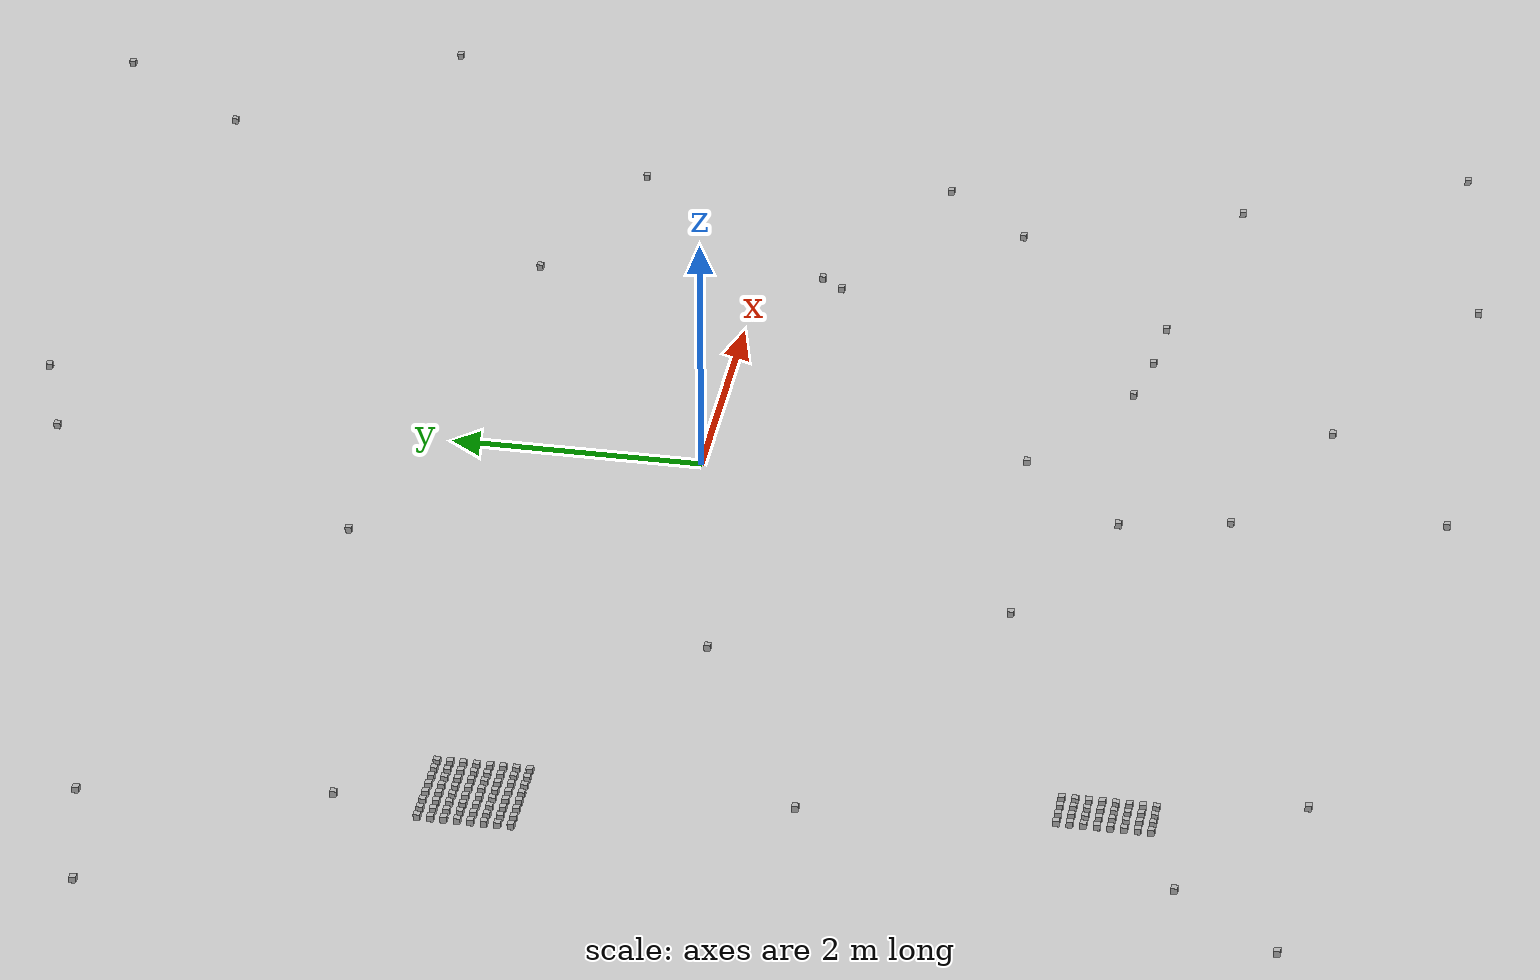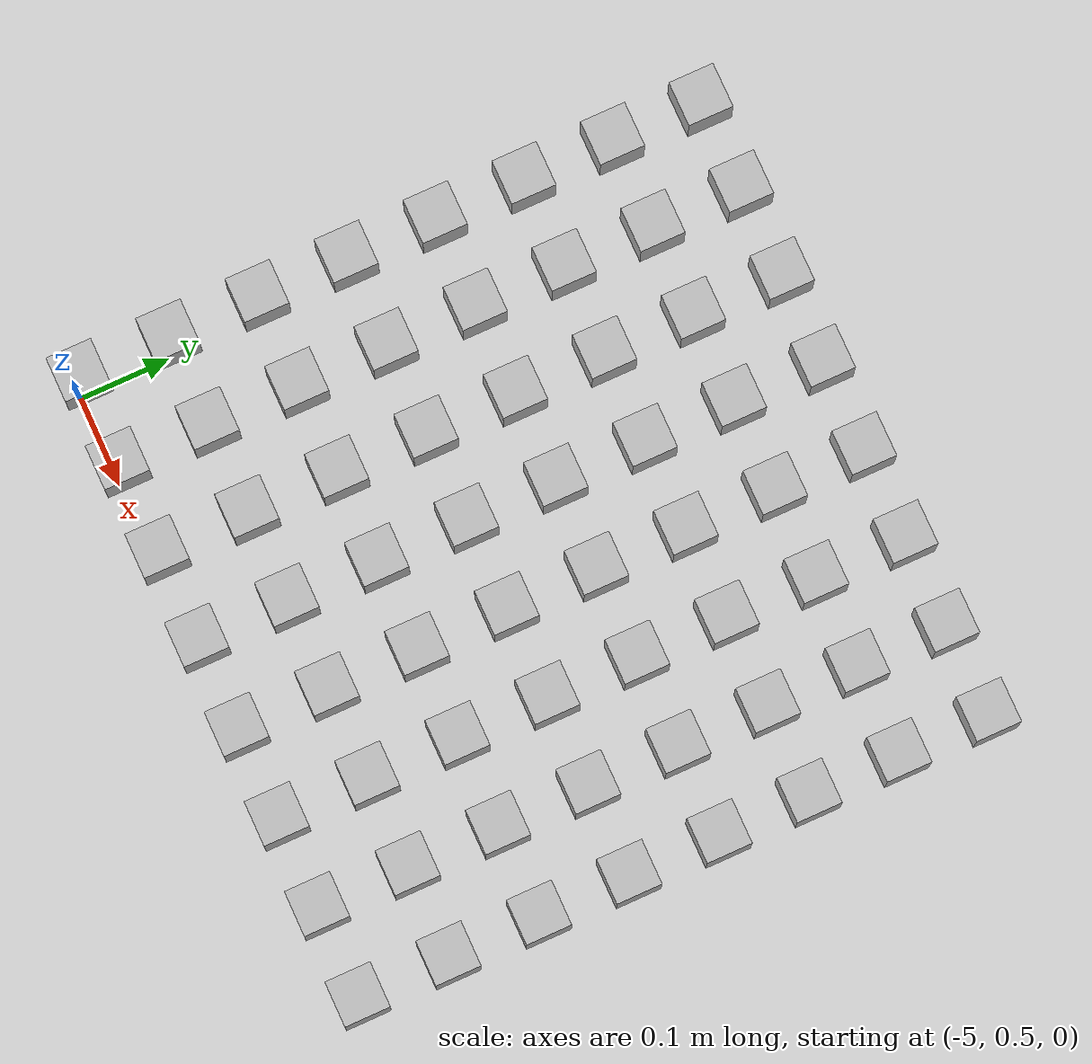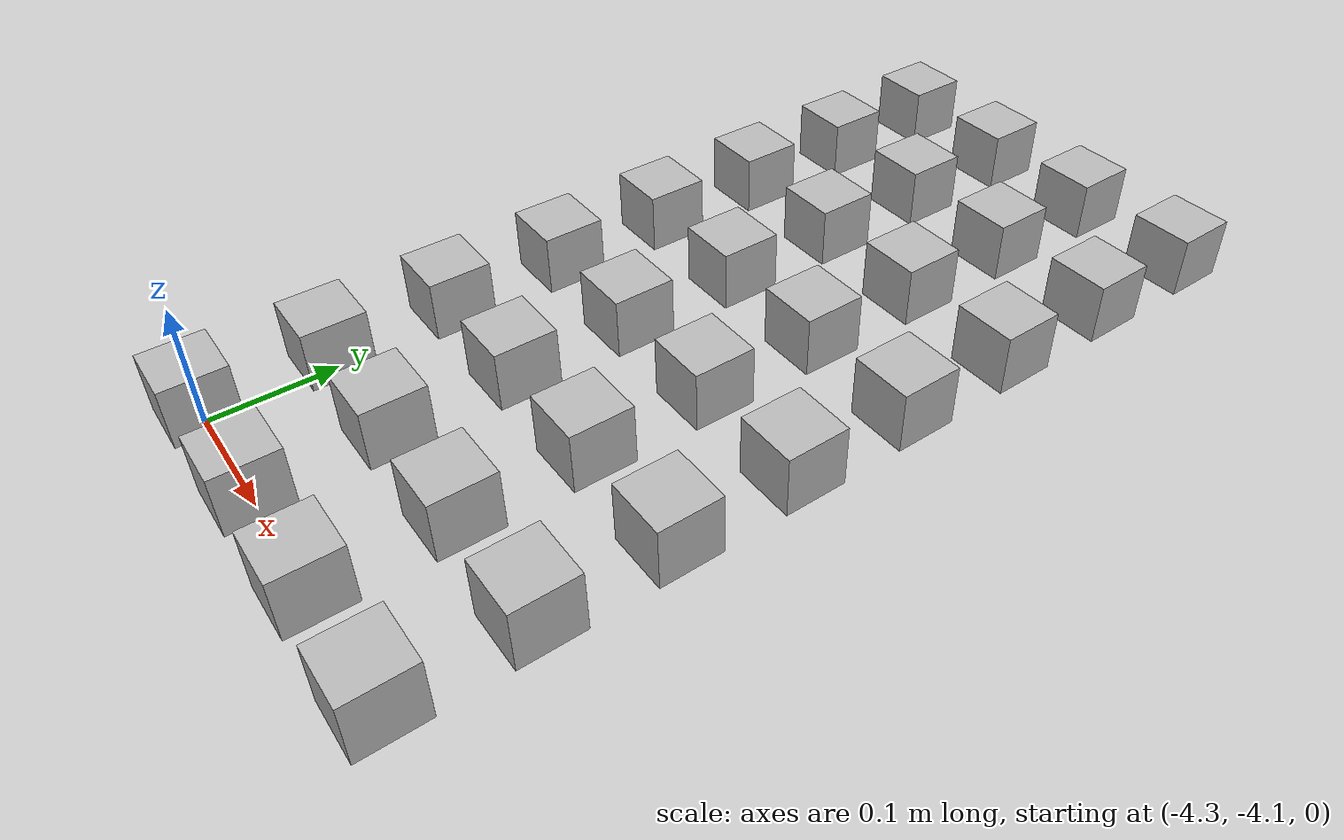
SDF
<sdf version="1.4">
 <world name="default">
  <model name="ground_plane">
   <static>1</static>
   <link name="link">
    <collision name="collision">
     <geometry><plane><normal>0 0 1</normal><size>100 100</size></plane></geometry>
     <surface><friction><ode><mu>100</mu><mu2>50</mu2></ode></friction></surface>
    </collision>
    <visual name="visual">
     <cast_shadows>0</cast_shadows>
     <geometry><plane><normal>0 0 1</normal><size>100 100</size></plane></geometry>
     <material>
      <script><uri>file://media/materials/scripts/gazebo.material</uri><name>Gazebo/Grey</name></script>
     </material>
    </visual>
    <velocity_decay><linear>0</linear><angular>0</angular></velocity_decay>
   </link>
  </model>
  <light name="sun" type="directional">
   <pose>0 0 10 0 -0 0</pose>
   <diffuse>0.8 0.8 0.8 1</diffuse>
   <specular>0.2 0.2 0.2 1</specular>
   <attenuation>
    <range>1000</range>
    <constant>0.9</constant>
    <linear>0.01</linear>
    <quadratic>0.001</quadratic>
   </attenuation>
   <direction>-0.5 0.1 -0.9</direction>
  </light>
  <plugin name="SetupWorld" filename="libgazebo_plugins.so"/>
  <physics type="ode">
   <max_step_size>0.001</max_step_size>
   <real_time_factor>1</real_time_factor>
   <real_time_update_rate>1000</real_time_update_rate>
   <gravity>0 0 -9.8</gravity>
  </physics>
  <scene><ambient>0.4 0.4 0.4 1</ambient><background>0.7 0.7 0.7 1</background><shadows>1</shadows></scene>
  <spherical_coordinates>
   <surface_model>EARTH_WGS84</surface_model>
   <latitude_deg>0</latitude_deg>
   <longitude_deg>0</longitude_deg>
   <elevation>0</elevation>
   <heading_deg>0</heading_deg>
  </spherical_coordinates>
  <model name="at0">
   <static>0</static>
   <link name="link">
    <inertial>
     <mass>0.01</mass>
     <inertia><ixx>4e-05</ixx><ixy>0</ixy><ixz>0</ixz><iyy>4e-05</iyy><iyz>0</iyz><izz>4e-05</izz></inertia>
    </inertial>
    <visual name="visual">
     <geometry><box><size>0.05 0.05 0.05</size></box></geometry>
     <material>
      <script>
       <uri>model://at0/materials/scripts</uri>
       <uri>model://at0/materials/textures</uri>
       <name>at0/Diffuse</name>
      </script>
     </material>
    </visual>
    <collision name="collision">
     <geometry><box><size>0.05 0.05 0.05</size></box></geometry>
     <surface><friction><ode><mu>0.8</mu><mu2>0.7</mu2></ode></friction></surface>
    </collision>
    <velocity_decay><linear>0</linear><angular>0</angular></velocity_decay>
   </link>
   <pose>-5.01833 0.509652 0.025 0 -0 0</pose>
  </model>
  <model name="at1">
   <static>0</static>
   <link name="link">
    <inertial>
     <mass>0.01</mass>
     <inertia><ixx>4e-05</ixx><ixy>0</ixy><ixz>0</ixz><iyy>4e-05</iyy><iyz>0</iyz><izz>4e-05</izz></inertia>
    </inertial>
    <visual name="visual">
     <geometry><box><size>0.05 0.05 0.05</size></box></geometry>
     <material>
      <script>
       <uri>model://at0/materials/scripts</uri>
       <uri>model://at0/materials/textures</uri>
       <name>at0/Diffuse</name>
      </script>
     </material>
    </visual>
    <collision name="collision">
     <geometry><box><size>0.05 0.05 0.05</size></box></geometry>
     <surface><friction><ode><mu>0.8</mu><mu2>0.7</mu2></ode></friction></surface>
    </collision>
    <velocity_decay><linear>0</linear><angular>0</angular></velocity_decay>
   </link>
   <pose>-4.91833 0.509652 0.025 0 -0 0</pose>
  </model>
  <model name="at2">
   <static>0</static>
   <link name="link">
    <inertial>
     <mass>0.01</mass>
     <inertia><ixx>4e-05</ixx><ixy>0</ixy><ixz>0</ixz><iyy>4e-05</iyy><iyz>0</iyz><izz>4e-05</izz></inertia>
    </inertial>
    <visual name="visual">
     <geometry><box><size>0.05 0.05 0.05</size></box></geometry>
     <material>
      <script>
       <uri>model://at0/materials/scripts</uri>
       <uri>model://at0/materials/textures</uri>
       <name>at0/Diffuse</name>
      </script>
     </material>
    </visual>
    <collision name="collision">
     <geometry><box><size>0.05 0.05 0.05</size></box></geometry>
     <surface><friction><ode><mu>0.8</mu><mu2>0.7</mu2></ode></friction></surface>
    </collision>
    <velocity_decay><linear>0</linear><angular>0</angular></velocity_decay>
   </link>
   <pose>-4.81833 0.509652 0.025 0 -0 0</pose>
  </model>
  <model name="at3">
   <static>0</static>
   <link name="link">
    <inertial>
     <mass>0.01</mass>
     <inertia><ixx>4e-05</ixx><ixy>0</ixy><ixz>0</ixz><iyy>4e-05</iyy><iyz>0</iyz><izz>4e-05</izz></inertia>
    </inertial>
    <visual name="visual">
     <geometry><box><size>0.05 0.05 0.05</size></box></geometry>
     <material>
      <script>
       <uri>model://at0/materials/scripts</uri>
       <uri>model://at0/materials/textures</uri>
       <name>at0/Diffuse</name>
      </script>
     </material>
    </visual>
    <collision name="collision">
     <geometry><box><size>0.05 0.05 0.05</size></box></geometry>
     <surface><friction><ode><mu>0.8</mu><mu2>0.7</mu2></ode></friction></surface>
    </collision>
    <velocity_decay><linear>0</linear><angular>0</angular></velocity_decay>
   </link>
   <pose>-4.71833 0.509652 0.025 0 -0 0</pose>
  </model>
  <model name="at4">
   <static>0</static>
   <link name="link">
    <inertial>
     <mass>0.01</mass>
     <inertia><ixx>4e-05</ixx><ixy>0</ixy><ixz>0</ixz><iyy>4e-05</iyy><iyz>0</iyz><izz>4e-05</izz></inertia>
    </inertial>
    <visual name="visual">
     <geometry><box><size>0.05 0.05 0.05</size></box></geometry>
     <material>
      <script>
       <uri>model://at0/materials/scripts</uri>
       <uri>model://at0/materials/textures</uri>
       <name>at0/Diffuse</name>
      </script>
     </material>
    </visual>
    <collision name="collision">
     <geometry><box><size>0.05 0.05 0.05</size></box></geometry>
     <surface><friction><ode><mu>0.8</mu><mu2>0.7</mu2></ode></friction></surface>
    </collision>
    <velocity_decay><linear>0</linear><angular>0</angular></velocity_decay>
   </link>
   <pose>-4.61833 0.509652 0.025 0 -0 0</pose>
  </model>
  <model name="at5">
   <static>0</static>
   <link name="link">
    <inertial>
     <mass>0.01</mass>
     <inertia><ixx>4e-05</ixx><ixy>0</ixy><ixz>0</ixz><iyy>4e-05</iyy><iyz>0</iyz><izz>4e-05</izz></inertia>
    </inertial>
    <visual name="visual">
     <geometry><box><size>0.05 0.05 0.05</size></box></geometry>
     <material>
      <script>
       <uri>model://at0/materials/scripts</uri>
       <uri>model://at0/materials/textures</uri>
       <name>at0/Diffuse</name>
      </script>
     </material>
    </visual>
    <collision name="collision">
     <geometry><box><size>0.05 0.05 0.05</size></box></geometry>
     <surface><friction><ode><mu>0.8</mu><mu2>0.7</mu2></ode></friction></surface>
    </collision>
    <velocity_decay><linear>0</linear><angular>0</angular></velocity_decay>
   </link>
   <pose>-4.51833 0.509652 0.025 0 -0 0</pose>
  </model>
  <model name="at6">
   <static>0</static>
   <link name="link">
    <inertial>
     <mass>0.01</mass>
     <inertia><ixx>4e-05</ixx><ixy>0</ixy><ixz>0</ixz><iyy>4e-05</iyy><iyz>0</iyz><izz>4e-05</izz></inertia>
    </inertial>
    <visual name="visual">
     <geometry><box><size>0.05 0.05 0.05</size></box></geometry>
     <material>
      <script>
       <uri>model://at0/materials/scripts</uri>
       <uri>model://at0/materials/textures</uri>
       <name>at0/Diffuse</name>
      </script>
     </material>
    </visual>
    <collision name="collision">
     <geometry><box><size>0.05 0.05 0.05</size></box></geometry>
     <surface><friction><ode><mu>0.8</mu><mu2>0.7</mu2></ode></friction></surface>
    </collision>
    <velocity_decay><linear>0</linear><angular>0</angular></velocity_decay>
   </link>
   <pose>-4.41833 0.509652 0.025 0 -0 0</pose>
  </model>
  <model name="at7">
   <static>0</static>
   <link name="link">
    <inertial>
     <mass>0.01</mass>
     <inertia><ixx>4e-05</ixx><ixy>0</ixy><ixz>0</ixz><iyy>4e-05</iyy><iyz>0</iyz><izz>4e-05</izz></inertia>
    </inertial>
    <visual name="visual">
     <geometry><box><size>0.05 0.05 0.05</size></box></geometry>
     <material>
      <script>
       <uri>model://at0/materials/scripts</uri>
       <uri>model://at0/materials/textures</uri>
       <name>at0/Diffuse</name>
      </script>
     </material>
    </visual>
    <collision name="collision">
     <geometry><box><size>0.05 0.05 0.05</size></box></geometry>
     <surface><friction><ode><mu>0.8</mu><mu2>0.7</mu2></ode></friction></surface>
    </collision>
    <velocity_decay><linear>0</linear><angular>0</angular></velocity_decay>
   </link>
   <pose>-4.31833 0.509652 0.025 0 -0 0</pose>
  </model>
  <model name="at8">
   <static>0</static>
   <link name="link">
    <inertial>
     <mass>0.01</mass>
     <inertia><ixx>4e-05</ixx><ixy>0</ixy><ixz>0</ixz><iyy>4e-05</iyy><iyz>0</iyz><izz>4e-05</izz></inertia>
    </inertial>
    <visual name="visual">
     <geometry><box><size>0.05 0.05 0.05</size></box></geometry>
     <material>
      <script>
       <uri>model://at0/materials/scripts</uri>
       <uri>model://at0/materials/textures</uri>
       <name>at0/Diffuse</name>
      </script>
     </material>
    </visual>
    <collision name="collision">
     <geometry><box><size>0.05 0.05 0.05</size></box></geometry>
     <surface><friction><ode><mu>0.8</mu><mu2>0.7</mu2></ode></friction></surface>
    </collision>
    <velocity_decay><linear>0</linear><angular>0</angular></velocity_decay>
   </link>
   <pose>-5.01833 0.609652 0.025 0 -0 0</pose>
  </model>
  <model name="at9">
   <static>0</static>
   <link name="link">
    <inertial>
     <mass>0.01</mass>
     <inertia><ixx>4e-05</ixx><ixy>0</ixy><ixz>0</ixz><iyy>4e-05</iyy><iyz>0</iyz><izz>4e-05</izz></inertia>
    </inertial>
    <visual name="visual">
     <geometry><box><size>0.05 0.05 0.05</size></box></geometry>
     <material>
      <script>
       <uri>model://at0/materials/scripts</uri>
       <uri>model://at0/materials/textures</uri>
       <name>at0/Diffuse</name>
      </script>
     </material>
    </visual>
    <collision name="collision">
     <geometry><box><size>0.05 0.05 0.05</size></box></geometry>
     <surface><friction><ode><mu>0.8</mu><mu2>0.7</mu2></ode></friction></surface>
    </collision>
    <velocity_decay><linear>0</linear><angular>0</angular></velocity_decay>
   </link>
   <pose>-4.91833 0.609652 0.025 0 -0 0</pose>
  </model>
  <model name="at10">
   <static>0</static>
   <link name="link">
    <inertial>
     <mass>0.01</mass>
     <inertia><ixx>4e-05</ixx><ixy>0</ixy><ixz>0</ixz><iyy>4e-05</iyy><iyz>0</iyz><izz>4e-05</izz></inertia>
    </inertial>
    <visual name="visual">
     <geometry><box><size>0.05 0.05 0.05</size></box></geometry>
     <material>
      <script>
       <uri>model://at0/materials/scripts</uri>
       <uri>model://at0/materials/textures</uri>
       <name>at0/Diffuse</name>
      </script>
     </material>
    </visual>
    <collision name="collision">
     <geometry><box><size>0.05 0.05 0.05</size></box></geometry>
     <surface><friction><ode><mu>0.8</mu><mu2>0.7</mu2></ode></friction></surface>
    </collision>
    <velocity_decay><linear>0</linear><angular>0</angular></velocity_decay>
   </link>
   <pose>-4.81833 0.609652 0.025 0 -0 0</pose>
  </model>
  <model name="at11">
   <static>0</static>
   <link name="link">
    <inertial>
     <mass>0.01</mass>
     <inertia><ixx>4e-05</ixx><ixy>0</ixy><ixz>0</ixz><iyy>4e-05</iyy><iyz>0</iyz><izz>4e-05</izz></inertia>
    </inertial>
    <visual name="visual">
     <geometry><box><size>0.05 0.05 0.05</size></box></geometry>
     <material>
      <script>
       <uri>model://at0/materials/scripts</uri>
       <uri>model://at0/materials/textures</uri>
       <name>at0/Diffuse</name>
      </script>
     </material>
    </visual>
    <collision name="collision">
     <geometry><box><size>0.05 0.05 0.05</size></box></geometry>
     <surface><friction><ode><mu>0.8</mu><mu2>0.7</mu2></ode></friction></surface>
    </collision>
    <velocity_decay><linear>0</linear><angular>0</angular></velocity_decay>
   </link>
   <pose>-4.71833 0.609652 0.025 0 -0 0</pose>
  </model>
  <model name="at12">
   <static>0</static>
   <link name="link">
    <inertial>
     <mass>0.01</mass>
     <inertia><ixx>4e-05</ixx><ixy>0</ixy><ixz>0</ixz><iyy>4e-05</iyy><iyz>0</iyz><izz>4e-05</izz></inertia>
    </inertial>
    <visual name="visual">
     <geometry><box><size>0.05 0.05 0.05</size></box></geometry>
     <material>
      <script>
       <uri>model://at0/materials/scripts</uri>
       <uri>model://at0/materials/textures</uri>
       <name>at0/Diffuse</name>
      </script>
     </material>
    </visual>
    <collision name="collision">
     <geometry><box><size>0.05 0.05 0.05</size></box></geometry>
     <surface><friction><ode><mu>0.8</mu><mu2>0.7</mu2></ode></friction></surface>
    </collision>
    <velocity_decay><linear>0</linear><angular>0</angular></velocity_decay>
   </link>
   <pose>-4.61833 0.609652 0.025 0 -0 0</pose>
  </model>
  <model name="at13">
   <static>0</static>
   <link name="link">
    <inertial>
     <mass>0.01</mass>
     <inertia><ixx>4e-05</ixx><ixy>0</ixy><ixz>0</ixz><iyy>4e-05</iyy><iyz>0</iyz><izz>4e-05</izz></inertia>
    </inertial>
    <visual name="visual">
     <geometry><box><size>0.05 0.05 0.05</size></box></geometry>
     <material>
      <script>
       <uri>model://at0/materials/scripts</uri>
       <uri>model://at0/materials/textures</uri>
       <name>at0/Diffuse</name>
      </script>
     </material>
    </visual>
    <collision name="collision">
     <geometry><box><size>0.05 0.05 0.05</size></box></geometry>
     <surface><friction><ode><mu>0.8</mu><mu2>0.7</mu2></ode></friction></surface>
    </collision>
    <velocity_decay><linear>0</linear><angular>0</angular></velocity_decay>
   </link>
   <pose>-4.51833 0.609652 0.025 0 -0 0</pose>
  </model>
  <model name="at14">
   <static>0</static>
   <link name="link">
    <inertial>
     <mass>0.01</mass>
     <inertia><ixx>4e-05</ixx><ixy>0</ixy><ixz>0</ixz><iyy>4e-05</iyy><iyz>0</iyz><izz>4e-05</izz></inertia>
    </inertial>
    <visual name="visual">
     <geometry><box><size>0.05 0.05 0.05</size></box></geometry>
     <material>
      <script>
       <uri>model://at0/materials/scripts</uri>
       <uri>model://at0/materials/textures</uri>
       <name>at0/Diffuse</name>
      </script>
     </material>
    </visual>
    <collision name="collision">
     <geometry><box><size>0.05 0.05 0.05</size></box></geometry>
     <surface><friction><ode><mu>0.8</mu><mu2>0.7</mu2></ode></friction></surface>
    </collision>
    <velocity_decay><linear>0</linear><angular>0</angular></velocity_decay>
   </link>
   <pose>-4.41833 0.609652 0.025 0 -0 0</pose>
  </model>
  <model name="at15">
   <static>0</static>
   <link name="link">
    <inertial>
     <mass>0.01</mass>
     <inertia><ixx>4e-05</ixx><ixy>0</ixy><ixz>0</ixz><iyy>4e-05</iyy><iyz>0</iyz><izz>4e-05</izz></inertia>
    </inertial>
    <visual name="visual">
     <geometry><box><size>0.05 0.05 0.05</size></box></geometry>
     <material>
      <script>
       <uri>model://at0/materials/scripts</uri>
       <uri>model://at0/materials/textures</uri>
       <name>at0/Diffuse</name>
      </script>
     </material>
    </visual>
    <collision name="collision">
     <geometry><box><size>0.05 0.05 0.05</size></box></geometry>
     <surface><friction><ode><mu>0.8</mu><mu2>0.7</mu2></ode></friction></surface>
    </collision>
    <velocity_decay><linear>0</linear><angular>0</angular></velocity_decay>
   </link>
   <pose>-4.31833 0.609652 0.025 0 -0 0</pose>
  </model>
  <model name="at16">
   <static>0</static>
   <link name="link">
    <inertial>
     <mass>0.01</mass>
     <inertia><ixx>4e-05</ixx><ixy>0</ixy><ixz>0</ixz><iyy>4e-05</iyy><iyz>0</iyz><izz>4e-05</izz></inertia>
    </inertial>
    <visual name="visual">
     <geometry><box><size>0.05 0.05 0.05</size></box></geometry>
     <material>
      <script>
       <uri>model://at0/materials/scripts</uri>
       <uri>model://at0/materials/textures</uri>
       <name>at0/Diffuse</name>
      </script>
     </material>
    </visual>
    <collision name="collision">
     <geometry><box><size>0.05 0.05 0.05</size></box></geometry>
     <surface><friction><ode><mu>0.8</mu><mu2>0.7</mu2></ode></friction></surface>
    </collision>
    <velocity_decay><linear>0</linear><angular>0</angular></velocity_decay>
   </link>
   <pose>-5.01833 0.709652 0.025 0 -0 0</pose>
  </model>
  <model name="at17">
   <static>0</static>
   <link name="link">
    <inertial>
     <mass>0.01</mass>
     <inertia><ixx>4e-05</ixx><ixy>0</ixy><ixz>0</ixz><iyy>4e-05</iyy><iyz>0</iyz><izz>4e-05</izz></inertia>
    </inertial>
    <visual name="visual">
     <geometry><box><size>0.05 0.05 0.05</size></box></geometry>
     <material>
      <script>
       <uri>model://at0/materials/scripts</uri>
       <uri>model://at0/materials/textures</uri>
       <name>at0/Diffuse</name>
      </script>
     </material>
    </visual>
    <collision name="collision">
     <geometry><box><size>0.05 0.05 0.05</size></box></geometry>
     <surface><friction><ode><mu>0.8</mu><mu2>0.7</mu2></ode></friction></surface>
    </collision>
    <velocity_decay><linear>0</linear><angular>0</angular></velocity_decay>
   </link>
   <pose>-4.91833 0.709652 0.025 0 -0 0</pose>
  </model>
  <model name="at18">
   <static>0</static>
   <link name="link">
    <inertial>
     <mass>0.01</mass>
     <inertia><ixx>4e-05</ixx><ixy>0</ixy><ixz>0</ixz><iyy>4e-05</iyy><iyz>0</iyz><izz>4e-05</izz></inertia>
    </inertial>
    <visual name="visual">
     <geometry><box><size>0.05 0.05 0.05</size></box></geometry>
     <material>
      <script>
       <uri>model://at0/materials/scripts</uri>
       <uri>model://at0/materials/textures</uri>
       <name>at0/Diffuse</name>
      </script>
     </material>
    </visual>
    <collision name="collision">
     <geometry><box><size>0.05 0.05 0.05</size></box></geometry>
     <surface><friction><ode><mu>0.8</mu><mu2>0.7</mu2></ode></friction></surface>
    </collision>
    <velocity_decay><linear>0</linear><angular>0</angular></velocity_decay>
   </link>
   <pose>-4.81833 0.709652 0.025 0 -0 0</pose>
  </model>
  <model name="at19">
   <static>0</static>
   <link name="link">
    <inertial>
     <mass>0.01</mass>
     <inertia><ixx>4e-05</ixx><ixy>0</ixy><ixz>0</ixz><iyy>4e-05</iyy><iyz>0</iyz><izz>4e-05</izz></inertia>
    </inertial>
    <visual name="visual">
     <geometry><box><size>0.05 0.05 0.05</size></box></geometry>
     <material>
      <script>
       <uri>model://at0/materials/scripts</uri>
       <uri>model://at0/materials/textures</uri>
       <name>at0/Diffuse</name>
      </script>
     </material>
    </visual>
    <collision name="collision">
     <geometry><box><size>0.05 0.05 0.05</size></box></geometry>
     <surface><friction><ode><mu>0.8</mu><mu2>0.7</mu2></ode></friction></surface>
    </collision>
    <velocity_decay><linear>0</linear><angular>0</angular></velocity_decay>
   </link>
   <pose>-4.71833 0.709652 0.025 0 -0 0</pose>
  </model>
  <model name="at20">
   <static>0</static>
   <link name="link">
    <inertial>
     <mass>0.01</mass>
     <inertia><ixx>4e-05</ixx><ixy>0</ixy><ixz>0</ixz><iyy>4e-05</iyy><iyz>0</iyz><izz>4e-05</izz></inertia>
    </inertial>
    <visual name="visual">
     <geometry><box><size>0.05 0.05 0.05</size></box></geometry>
     <material>
      <script>
       <uri>model://at0/materials/scripts</uri>
       <uri>model://at0/materials/textures</uri>
       <name>at0/Diffuse</name>
      </script>
     </material>
    </visual>
    <collision name="collision">
     <geometry><box><size>0.05 0.05 0.05</size></box></geometry>
     <surface><friction><ode><mu>0.8</mu><mu2>0.7</mu2></ode></friction></surface>
    </collision>
    <velocity_decay><linear>0</linear><angular>0</angular></velocity_decay>
   </link>
   <pose>-4.61833 0.709652 0.025 0 -0 0</pose>
  </model>
  <model name="at21">
   <static>0</static>
   <link name="link">
    <inertial>
     <mass>0.01</mass>
     <inertia><ixx>4e-05</ixx><ixy>0</ixy><ixz>0</ixz><iyy>4e-05</iyy><iyz>0</iyz><izz>4e-05</izz></inertia>
    </inertial>
    <visual name="visual">
     <geometry><box><size>0.05 0.05 0.05</size></box></geometry>
     <material>
      <script>
       <uri>model://at0/materials/scripts</uri>
       <uri>model://at0/materials/textures</uri>
       <name>at0/Diffuse</name>
      </script>
     </material>
    </visual>
    <collision name="collision">
     <geometry><box><size>0.05 0.05 0.05</size></box></geometry>
     <surface><friction><ode><mu>0.8</mu><mu2>0.7</mu2></ode></friction></surface>
    </collision>
    <velocity_decay><linear>0</linear><angular>0</angular></velocity_decay>
   </link>
   <pose>-4.51833 0.709652 0.025 0 -0 0</pose>
  </model>
  <model name="at22">
   <static>0</static>
   <link name="link">
    <inertial>
     <mass>0.01</mass>
     <inertia><ixx>4e-05</ixx><ixy>0</ixy><ixz>0</ixz><iyy>4e-05</iyy><iyz>0</iyz><izz>4e-05</izz></inertia>
    </inertial>
    <visual name="visual">
     <geometry><box><size>0.05 0.05 0.05</size></box></geometry>
     <material>
      <script>
       <uri>model://at0/materials/scripts</uri>
       <uri>model://at0/materials/textures</uri>
       <name>at0/Diffuse</name>
      </script>
     </material>
    </visual>
    <collision name="collision">
     <geometry><box><size>0.05 0.05 0.05</size></box></geometry>
     <surface><friction><ode><mu>0.8</mu><mu2>0.7</mu2></ode></friction></surface>
    </collision>
    <velocity_decay><linear>0</linear><angular>0</angular></velocity_decay>
   </link>
   <pose>-4.41833 0.709652 0.025 0 -0 0</pose>
  </model>
  <model name="at23">
   <static>0</static>
   <link name="link">
    <inertial>
     <mass>0.01</mass>
     <inertia><ixx>4e-05</ixx><ixy>0</ixy><ixz>0</ixz><iyy>4e-05</iyy><iyz>0</iyz><izz>4e-05</izz></inertia>
    </inertial>
    <visual name="visual">
     <geometry><box><size>0.05 0.05 0.05</size></box></geometry>
     <material>
      <script>
       <uri>model://at0/materials/scripts</uri>
       <uri>model://at0/materials/textures</uri>
       <name>at0/Diffuse</name>
      </script>
     </material>
    </visual>
    <collision name="collision">
     <geometry><box><size>0.05 0.05 0.05</size></box></geometry>
     <surface><friction><ode><mu>0.8</mu><mu2>0.7</mu2></ode></friction></surface>
    </collision>
    <velocity_decay><linear>0</linear><angular>0</angular></velocity_decay>
   </link>
   <pose>-4.31833 0.709652 0.025 0 -0 0</pose>
  </model>
  <model name="at24">
   <static>0</static>
   <link name="link">
    <inertial>
     <mass>0.01</mass>
     <inertia><ixx>4e-05</ixx><ixy>0</ixy><ixz>0</ixz><iyy>4e-05</iyy><iyz>0</iyz><izz>4e-05</izz></inertia>
    </inertial>
    <visual name="visual">
     <geometry><box><size>0.05 0.05 0.05</size></box></geometry>
     <material>
      <script>
       <uri>model://at0/materials/scripts</uri>
       <uri>model://at0/materials/textures</uri>
       <name>at0/Diffuse</name>
      </script>
     </material>
    </visual>
    <collision name="collision">
     <geometry><box><size>0.05 0.05 0.05</size></box></geometry>
     <surface><friction><ode><mu>0.8</mu><mu2>0.7</mu2></ode></friction></surface>
    </collision>
    <velocity_decay><linear>0</linear><angular>0</angular></velocity_decay>
   </link>
   <pose>-5.01833 0.809652 0.025 0 -0 0</pose>
  </model>
  <model name="at25">
   <static>0</static>
   <link name="link">
    <inertial>
     <mass>0.01</mass>
     <inertia><ixx>4e-05</ixx><ixy>0</ixy><ixz>0</ixz><iyy>4e-05</iyy><iyz>0</iyz><izz>4e-05</izz></inertia>
    </inertial>
    <visual name="visual">
     <geometry><box><size>0.05 0.05 0.05</size></box></geometry>
     <material>
      <script>
       <uri>model://at0/materials/scripts</uri>
       <uri>model://at0/materials/textures</uri>
       <name>at0/Diffuse</name>
      </script>
     </material>
    </visual>
    <collision name="collision">
     <geometry><box><size>0.05 0.05 0.05</size></box></geometry>
     <surface><friction><ode><mu>0.8</mu><mu2>0.7</mu2></ode></friction></surface>
    </collision>
    <velocity_decay><linear>0</linear><angular>0</angular></velocity_decay>
   </link>
   <pose>-4.91833 0.809652 0.025 0 -0 0</pose>
  </model>
  <model name="at26">
   <static>0</static>
   <link name="link">
    <inertial>
     <mass>0.01</mass>
     <inertia><ixx>4e-05</ixx><ixy>0</ixy><ixz>0</ixz><iyy>4e-05</iyy><iyz>0</iyz><izz>4e-05</izz></inertia>
    </inertial>
    <visual name="visual">
     <geometry><box><size>0.05 0.05 0.05</size></box></geometry>
     <material>
      <script>
       <uri>model://at0/materials/scripts</uri>
       <uri>model://at0/materials/textures</uri>
       <name>at0/Diffuse</name>
      </script>
     </material>
    </visual>
    <collision name="collision">
     <geometry><box><size>0.05 0.05 0.05</size></box></geometry>
     <surface><friction><ode><mu>0.8</mu><mu2>0.7</mu2></ode></friction></surface>
    </collision>
    <velocity_decay><linear>0</linear><angular>0</angular></velocity_decay>
   </link>
   <pose>-4.81833 0.809652 0.025 0 -0 0</pose>
  </model>
  <model name="at27">
   <static>0</static>
   <link name="link">
    <inertial>
     <mass>0.01</mass>
     <inertia><ixx>4e-05</ixx><ixy>0</ixy><ixz>0</ixz><iyy>4e-05</iyy><iyz>0</iyz><izz>4e-05</izz></inertia>
    </inertial>
    <visual name="visual">
     <geometry><box><size>0.05 0.05 0.05</size></box></geometry>
     <material>
      <script>
       <uri>model://at0/materials/scripts</uri>
       <uri>model://at0/materials/textures</uri>
       <name>at0/Diffuse</name>
      </script>
     </material>
    </visual>
    <collision name="collision">
     <geometry><box><size>0.05 0.05 0.05</size></box></geometry>
     <surface><friction><ode><mu>0.8</mu><mu2>0.7</mu2></ode></friction></surface>
    </collision>
    <velocity_decay><linear>0</linear><angular>0</angular></velocity_decay>
   </link>
   <pose>-4.71833 0.809652 0.025 0 -0 0</pose>
  </model>
  <model name="at28">
   <static>0</static>
   <link name="link">
    <inertial>
     <mass>0.01</mass>
     <inertia><ixx>4e-05</ixx><ixy>0</ixy><ixz>0</ixz><iyy>4e-05</iyy><iyz>0</iyz><izz>4e-05</izz></inertia>
    </inertial>
    <visual name="visual">
     <geometry><box><size>0.05 0.05 0.05</size></box></geometry>
     <material>
      <script>
       <uri>model://at0/materials/scripts</uri>
       <uri>model://at0/materials/textures</uri>
       <name>at0/Diffuse</name>
      </script>
     </material>
    </visual>
    <collision name="collision">
     <geometry><box><size>0.05 0.05 0.05</size></box></geometry>
     <surface><friction><ode><mu>0.8</mu><mu2>0.7</mu2></ode></friction></surface>
    </collision>
    <velocity_decay><linear>0</linear><angular>0</angular></velocity_decay>
   </link>
   <pose>-4.61833 0.809652 0.025 0 -0 0</pose>
  </model>
  <model name="at29">
   <static>0</static>
   <link name="link">
    <inertial>
     <mass>0.01</mass>
     <inertia><ixx>4e-05</ixx><ixy>0</ixy><ixz>0</ixz><iyy>4e-05</iyy><iyz>0</iyz><izz>4e-05</izz></inertia>
    </inertial>
    <visual name="visual">
     <geometry><box><size>0.05 0.05 0.05</size></box></geometry>
     <material>
      <script>
       <uri>model://at0/materials/scripts</uri>
       <uri>model://at0/materials/textures</uri>
       <name>at0/Diffuse</name>
      </script>
     </material>
    </visual>
    <collision name="collision">
     <geometry><box><size>0.05 0.05 0.05</size></box></geometry>
     <surface><friction><ode><mu>0.8</mu><mu2>0.7</mu2></ode></friction></surface>
    </collision>
    <velocity_decay><linear>0</linear><angular>0</angular></velocity_decay>
   </link>
   <pose>-4.51833 0.809652 0.025 0 -0 0</pose>
  </model>
  <model name="at30">
   <static>0</static>
   <link name="link">
    <inertial>
     <mass>0.01</mass>
     <inertia><ixx>4e-05</ixx><ixy>0</ixy><ixz>0</ixz><iyy>4e-05</iyy><iyz>0</iyz><izz>4e-05</izz></inertia>
    </inertial>
    <visual name="visual">
     <geometry><box><size>0.05 0.05 0.05</size></box></geometry>
     <material>
      <script>
       <uri>model://at0/materials/scripts</uri>
       <uri>model://at0/materials/textures</uri>
       <name>at0/Diffuse</name>
      </script>
     </material>
    </visual>
    <collision name="collision">
     <geometry><box><size>0.05 0.05 0.05</size></box></geometry>
     <surface><friction><ode><mu>0.8</mu><mu2>0.7</mu2></ode></friction></surface>
    </collision>
    <velocity_decay><linear>0</linear><angular>0</angular></velocity_decay>
   </link>
   <pose>-4.41833 0.809652 0.025 0 -0 0</pose>
  </model>
  <model name="at31">
   <static>0</static>
   <link name="link">
    <inertial>
     <mass>0.01</mass>
     <inertia><ixx>4e-05</ixx><ixy>0</ixy><ixz>0</ixz><iyy>4e-05</iyy><iyz>0</iyz><izz>4e-05</izz></inertia>
    </inertial>
    <visual name="visual">
     <geometry><box><size>0.05 0.05 0.05</size></box></geometry>
     <material>
      <script>
       <uri>model://at0/materials/scripts</uri>
       <uri>model://at0/materials/textures</uri>
       <name>at0/Diffuse</name>
      </script>
     </material>
    </visual>
    <collision name="collision">
     <geometry><box><size>0.05 0.05 0.05</size></box></geometry>
     <surface><friction><ode><mu>0.8</mu><mu2>0.7</mu2></ode></friction></surface>
    </collision>
    <velocity_decay><linear>0</linear><angular>0</angular></velocity_decay>
   </link>
   <pose>-4.31833 0.809652 0.025 0 -0 0</pose>
  </model>
  <model name="at32">
   <static>0</static>
   <link name="link">
    <inertial>
     <mass>0.01</mass>
     <inertia><ixx>4e-05</ixx><ixy>0</ixy><ixz>0</ixz><iyy>4e-05</iyy><iyz>0</iyz><izz>4e-05</izz></inertia>
    </inertial>
    <visual name="visual">
     <geometry><box><size>0.05 0.05 0.05</size></box></geometry>
     <material>
      <script>
       <uri>model://at0/materials/scripts</uri>
       <uri>model://at0/materials/textures</uri>
       <name>at0/Diffuse</name>
      </script>
     </material>
    </visual>
    <collision name="collision">
     <geometry><box><size>0.05 0.05 0.05</size></box></geometry>
     <surface><friction><ode><mu>0.8</mu><mu2>0.7</mu2></ode></friction></surface>
    </collision>
    <velocity_decay><linear>0</linear><angular>0</angular></velocity_decay>
   </link>
   <pose>-5.01833 0.909652 0.025 0 -0 0</pose>
  </model>
  <model name="at33">
   <static>0</static>
   <link name="link">
    <inertial>
     <mass>0.01</mass>
     <inertia><ixx>4e-05</ixx><ixy>0</ixy><ixz>0</ixz><iyy>4e-05</iyy><iyz>0</iyz><izz>4e-05</izz></inertia>
    </inertial>
    <visual name="visual">
     <geometry><box><size>0.05 0.05 0.05</size></box></geometry>
     <material>
      <script>
       <uri>model://at0/materials/scripts</uri>
       <uri>model://at0/materials/textures</uri>
       <name>at0/Diffuse</name>
      </script>
     </material>
    </visual>
    <collision name="collision">
     <geometry><box><size>0.05 0.05 0.05</size></box></geometry>
     <surface><friction><ode><mu>0.8</mu><mu2>0.7</mu2></ode></friction></surface>
    </collision>
    <velocity_decay><linear>0</linear><angular>0</angular></velocity_decay>
   </link>
   <pose>-4.91833 0.909652 0.025 0 -0 0</pose>
  </model>
  <model name="at34">
   <static>0</static>
   <link name="link">
    <inertial>
     <mass>0.01</mass>
     <inertia><ixx>4e-05</ixx><ixy>0</ixy><ixz>0</ixz><iyy>4e-05</iyy><iyz>0</iyz><izz>4e-05</izz></inertia>
    </inertial>
    <visual name="visual">
     <geometry><box><size>0.05 0.05 0.05</size></box></geometry>
     <material>
      <script>
       <uri>model://at0/materials/scripts</uri>
       <uri>model://at0/materials/textures</uri>
       <name>at0/Diffuse</name>
      </script>
     </material>
    </visual>
    <collision name="collision">
     <geometry><box><size>0.05 0.05 0.05</size></box></geometry>
     <surface><friction><ode><mu>0.8</mu><mu2>0.7</mu2></ode></friction></surface>
    </collision>
    <velocity_decay><linear>0</linear><angular>0</angular></velocity_decay>
   </link>
   <pose>-4.81833 0.909652 0.025 0 -0 0</pose>
  </model>
  <model name="at35">
   <static>0</static>
   <link name="link">
    <inertial>
     <mass>0.01</mass>
     <inertia><ixx>4e-05</ixx><ixy>0</ixy><ixz>0</ixz><iyy>4e-05</iyy><iyz>0</iyz><izz>4e-05</izz></inertia>
    </inertial>
    <visual name="visual">
     <geometry><box><size>0.05 0.05 0.05</size></box></geometry>
     <material>
      <script>
       <uri>model://at0/materials/scripts</uri>
       <uri>model://at0/materials/textures</uri>
       <name>at0/Diffuse</name>
      </script>
     </material>
    </visual>
    <collision name="collision">
     <geometry><box><size>0.05 0.05 0.05</size></box></geometry>
     <surface><friction><ode><mu>0.8</mu><mu2>0.7</mu2></ode></friction></surface>
    </collision>
    <velocity_decay><linear>0</linear><angular>0</angular></velocity_decay>
   </link>
   <pose>-4.71833 0.909652 0.025 0 -0 0</pose>
  </model>
  <model name="at36">
   <static>0</static>
   <link name="link">
    <inertial>
     <mass>0.01</mass>
     <inertia><ixx>4e-05</ixx><ixy>0</ixy><ixz>0</ixz><iyy>4e-05</iyy><iyz>0</iyz><izz>4e-05</izz></inertia>
    </inertial>
    <visual name="visual">
     <geometry><box><size>0.05 0.05 0.05</size></box></geometry>
     <material>
      <script>
       <uri>model://at0/materials/scripts</uri>
       <uri>model://at0/materials/textures</uri>
       <name>at0/Diffuse</name>
      </script>
     </material>
    </visual>
    <collision name="collision">
     <geometry><box><size>0.05 0.05 0.05</size></box></geometry>
     <surface><friction><ode><mu>0.8</mu><mu2>0.7</mu2></ode></friction></surface>
    </collision>
    <velocity_decay><linear>0</linear><angular>0</angular></velocity_decay>
   </link>
   <pose>-4.61833 0.909652 0.025 0 -0 0</pose>
  </model>
  <model name="at37">
   <static>0</static>
   <link name="link">
    <inertial>
     <mass>0.01</mass>
     <inertia><ixx>4e-05</ixx><ixy>0</ixy><ixz>0</ixz><iyy>4e-05</iyy><iyz>0</iyz><izz>4e-05</izz></inertia>
    </inertial>
    <visual name="visual">
     <geometry><box><size>0.05 0.05 0.05</size></box></geometry>
     <material>
      <script>
       <uri>model://at0/materials/scripts</uri>
       <uri>model://at0/materials/textures</uri>
       <name>at0/Diffuse</name>
      </script>
     </material>
    </visual>
    <collision name="collision">
     <geometry><box><size>0.05 0.05 0.05</size></box></geometry>
     <surface><friction><ode><mu>0.8</mu><mu2>0.7</mu2></ode></friction></surface>
    </collision>
    <velocity_decay><linear>0</linear><angular>0</angular></velocity_decay>
   </link>
   <pose>-4.51833 0.909652 0.025 0 -0 0</pose>
  </model>
  <model name="at38">
   <static>0</static>
   <link name="link">
    <inertial>
     <mass>0.01</mass>
     <inertia><ixx>4e-05</ixx><ixy>0</ixy><ixz>0</ixz><iyy>4e-05</iyy><iyz>0</iyz><izz>4e-05</izz></inertia>
    </inertial>
    <visual name="visual">
     <geometry><box><size>0.05 0.05 0.05</size></box></geometry>
     <material>
      <script>
       <uri>model://at0/materials/scripts</uri>
       <uri>model://at0/materials/textures</uri>
       <name>at0/Diffuse</name>
      </script>
     </material>
    </visual>
    <collision name="collision">
     <geometry><box><size>0.05 0.05 0.05</size></box></geometry>
     <surface><friction><ode><mu>0.8</mu><mu2>0.7</mu2></ode></friction></surface>
    </collision>
    <velocity_decay><linear>0</linear><angular>0</angular></velocity_decay>
   </link>
   <pose>-4.41833 0.909652 0.025 0 -0 0</pose>
  </model>
  <model name="at39">
   <static>0</static>
   <link name="link">
    <inertial>
     <mass>0.01</mass>
     <inertia><ixx>4e-05</ixx><ixy>0</ixy><ixz>0</ixz><iyy>4e-05</iyy><iyz>0</iyz><izz>4e-05</izz></inertia>
    </inertial>
    <visual name="visual">
     <geometry><box><size>0.05 0.05 0.05</size></box></geometry>
     <material>
      <script>
       <uri>model://at0/materials/scripts</uri>
       <uri>model://at0/materials/textures</uri>
       <name>at0/Diffuse</name>
      </script>
     </material>
    </visual>
    <collision name="collision">
     <geometry><box><size>0.05 0.05 0.05</size></box></geometry>
     <surface><friction><ode><mu>0.8</mu><mu2>0.7</mu2></ode></friction></surface>
    </collision>
    <velocity_decay><linear>0</linear><angular>0</angular></velocity_decay>
   </link>
   <pose>-4.31833 0.909652 0.025 0 -0 0</pose>
  </model>
  <model name="at40">
   <static>0</static>
   <link name="link">
    <inertial>
     <mass>0.01</mass>
     <inertia><ixx>4e-05</ixx><ixy>0</ixy><ixz>0</ixz><iyy>4e-05</iyy><iyz>0</iyz><izz>4e-05</izz></inertia>
    </inertial>
    <visual name="visual">
     <geometry><box><size>0.05 0.05 0.05</size></box></geometry>
     <material>
      <script>
       <uri>model://at0/materials/scripts</uri>
       <uri>model://at0/materials/textures</uri>
       <name>at0/Diffuse</name>
      </script>
     </material>
    </visual>
    <collision name="collision">
     <geometry><box><size>0.05 0.05 0.05</size></box></geometry>
     <surface><friction><ode><mu>0.8</mu><mu2>0.7</mu2></ode></friction></surface>
    </collision>
    <velocity_decay><linear>0</linear><angular>0</angular></velocity_decay>
   </link>
   <pose>-5.01833 1.00965 0.025 0 -0 0</pose>
  </model>
  <model name="at41">
   <static>0</static>
   <link name="link">
    <inertial>
     <mass>0.01</mass>
     <inertia><ixx>4e-05</ixx><ixy>0</ixy><ixz>0</ixz><iyy>4e-05</iyy><iyz>0</iyz><izz>4e-05</izz></inertia>
    </inertial>
    <visual name="visual">
     <geometry><box><size>0.05 0.05 0.05</size></box></geometry>
     <material>
      <script>
       <uri>model://at0/materials/scripts</uri>
       <uri>model://at0/materials/textures</uri>
       <name>at0/Diffuse</name>
      </script>
     </material>
    </visual>
    <collision name="collision">
     <geometry><box><size>0.05 0.05 0.05</size></box></geometry>
     <surface><friction><ode><mu>0.8</mu><mu2>0.7</mu2></ode></friction></surface>
    </collision>
    <velocity_decay><linear>0</linear><angular>0</angular></velocity_decay>
   </link>
   <pose>-4.91833 1.00965 0.025 0 -0 0</pose>
  </model>
  <model name="at42">
   <static>0</static>
   <link name="link">
    <inertial>
     <mass>0.01</mass>
     <inertia><ixx>4e-05</ixx><ixy>0</ixy><ixz>0</ixz><iyy>4e-05</iyy><iyz>0</iyz><izz>4e-05</izz></inertia>
    </inertial>
    <visual name="visual">
     <geometry><box><size>0.05 0.05 0.05</size></box></geometry>
     <material>
      <script>
       <uri>model://at0/materials/scripts</uri>
       <uri>model://at0/materials/textures</uri>
       <name>at0/Diffuse</name>
      </script>
     </material>
    </visual>
    <collision name="collision">
     <geometry><box><size>0.05 0.05 0.05</size></box></geometry>
     <surface><friction><ode><mu>0.8</mu><mu2>0.7</mu2></ode></friction></surface>
    </collision>
    <velocity_decay><linear>0</linear><angular>0</angular></velocity_decay>
   </link>
   <pose>-4.81833 1.00965 0.025 0 -0 0</pose>
  </model>
  <model name="at43">
   <static>0</static>
   <link name="link">
    <inertial>
     <mass>0.01</mass>
     <inertia><ixx>4e-05</ixx><ixy>0</ixy><ixz>0</ixz><iyy>4e-05</iyy><iyz>0</iyz><izz>4e-05</izz></inertia>
    </inertial>
    <visual name="visual">
     <geometry><box><size>0.05 0.05 0.05</size></box></geometry>
     <material>
      <script>
       <uri>model://at0/materials/scripts</uri>
       <uri>model://at0/materials/textures</uri>
       <name>at0/Diffuse</name>
      </script>
     </material>
    </visual>
    <collision name="collision">
     <geometry><box><size>0.05 0.05 0.05</size></box></geometry>
     <surface><friction><ode><mu>0.8</mu><mu2>0.7</mu2></ode></friction></surface>
    </collision>
    <velocity_decay><linear>0</linear><angular>0</angular></velocity_decay>
   </link>
   <pose>-4.71833 1.00965 0.025 0 -0 0</pose>
  </model>
  <model name="at44">
   <static>0</static>
   <link name="link">
    <inertial>
     <mass>0.01</mass>
     <inertia><ixx>4e-05</ixx><ixy>0</ixy><ixz>0</ixz><iyy>4e-05</iyy><iyz>0</iyz><izz>4e-05</izz></inertia>
    </inertial>
    <visual name="visual">
     <geometry><box><size>0.05 0.05 0.05</size></box></geometry>
     <material>
      <script>
       <uri>model://at0/materials/scripts</uri>
       <uri>model://at0/materials/textures</uri>
       <name>at0/Diffuse</name>
      </script>
     </material>
    </visual>
    <collision name="collision">
     <geometry><box><size>0.05 0.05 0.05</size></box></geometry>
     <surface><friction><ode><mu>0.8</mu><mu2>0.7</mu2></ode></friction></surface>
    </collision>
    <velocity_decay><linear>0</linear><angular>0</angular></velocity_decay>
   </link>
   <pose>-4.61833 1.00965 0.025 0 -0 0</pose>
  </model>
  <model name="at45">
   <static>0</static>
   <link name="link">
    <inertial>
     <mass>0.01</mass>
     <inertia><ixx>4e-05</ixx><ixy>0</ixy><ixz>0</ixz><iyy>4e-05</iyy><iyz>0</iyz><izz>4e-05</izz></inertia>
    </inertial>
    <visual name="visual">
     <geometry><box><size>0.05 0.05 0.05</size></box></geometry>
     <material>
      <script>
       <uri>model://at0/materials/scripts</uri>
       <uri>model://at0/materials/textures</uri>
       <name>at0/Diffuse</name>
      </script>
     </material>
    </visual>
    <collision name="collision">
     <geometry><box><size>0.05 0.05 0.05</size></box></geometry>
     <surface><friction><ode><mu>0.8</mu><mu2>0.7</mu2></ode></friction></surface>
    </collision>
    <velocity_decay><linear>0</linear><angular>0</angular></velocity_decay>
   </link>
   <pose>-4.51833 1.00965 0.025 0 -0 0</pose>
  </model>
  <model name="at46">
   <static>0</static>
   <link name="link">
    <inertial>
     <mass>0.01</mass>
     <inertia><ixx>4e-05</ixx><ixy>0</ixy><ixz>0</ixz><iyy>4e-05</iyy><iyz>0</iyz><izz>4e-05</izz></inertia>
    </inertial>
    <visual name="visual">
     <geometry><box><size>0.05 0.05 0.05</size></box></geometry>
     <material>
      <script>
       <uri>model://at0/materials/scripts</uri>
       <uri>model://at0/materials/textures</uri>
       <name>at0/Diffuse</name>
      </script>
     </material>
    </visual>
    <collision name="collision">
     <geometry><box><size>0.05 0.05 0.05</size></box></geometry>
     <surface><friction><ode><mu>0.8</mu><mu2>0.7</mu2></ode></friction></surface>
    </collision>
    <velocity_decay><linear>0</linear><angular>0</angular></velocity_decay>
   </link>
   <pose>-4.41833 1.00965 0.025 0 -0 0</pose>
  </model>
  <model name="at47">
   <static>0</static>
   <link name="link">
    <inertial>
     <mass>0.01</mass>
     <inertia><ixx>4e-05</ixx><ixy>0</ixy><ixz>0</ixz><iyy>4e-05</iyy><iyz>0</iyz><izz>4e-05</izz></inertia>
    </inertial>
    <visual name="visual">
     <geometry><box><size>0.05 0.05 0.05</size></box></geometry>
     <material>
      <script>
       <uri>model://at0/materials/scripts</uri>
       <uri>model://at0/materials/textures</uri>
       <name>at0/Diffuse</name>
      </script>
     </material>
    </visual>
    <collision name="collision">
     <geometry><box><size>0.05 0.05 0.05</size></box></geometry>
     <surface><friction><ode><mu>0.8</mu><mu2>0.7</mu2></ode></friction></surface>
    </collision>
    <velocity_decay><linear>0</linear><angular>0</angular></velocity_decay>
   </link>
   <pose>-4.31833 1.00965 0.025 0 -0 0</pose>
  </model>
  <model name="at48">
   <static>0</static>
   <link name="link">
    <inertial>
     <mass>0.01</mass>
     <inertia><ixx>4e-05</ixx><ixy>0</ixy><ixz>0</ixz><iyy>4e-05</iyy><iyz>0</iyz><izz>4e-05</izz></inertia>
    </inertial>
    <visual name="visual">
     <geometry><box><size>0.05 0.05 0.05</size></box></geometry>
     <material>
      <script>
       <uri>model://at0/materials/scripts</uri>
       <uri>model://at0/materials/textures</uri>
       <name>at0/Diffuse</name>
      </script>
     </material>
    </visual>
    <collision name="collision">
     <geometry><box><size>0.05 0.05 0.05</size></box></geometry>
     <surface><friction><ode><mu>0.8</mu><mu2>0.7</mu2></ode></friction></surface>
    </collision>
    <velocity_decay><linear>0</linear><angular>0</angular></velocity_decay>
   </link>
   <pose>-5.01833 1.10965 0.025 0 -0 0</pose>
  </model>
  <model name="at49">
   <static>0</static>
   <link name="link">
    <inertial>
     <mass>0.01</mass>
     <inertia><ixx>4e-05</ixx><ixy>0</ixy><ixz>0</ixz><iyy>4e-05</iyy><iyz>0</iyz><izz>4e-05</izz></inertia>
    </inertial>
    <visual name="visual">
     <geometry><box><size>0.05 0.05 0.05</size></box></geometry>
     <material>
      <script>
       <uri>model://at0/materials/scripts</uri>
       <uri>model://at0/materials/textures</uri>
       <name>at0/Diffuse</name>
      </script>
     </material>
    </visual>
    <collision name="collision">
     <geometry><box><size>0.05 0.05 0.05</size></box></geometry>
     <surface><friction><ode><mu>0.8</mu><mu2>0.7</mu2></ode></friction></surface>
    </collision>
    <velocity_decay><linear>0</linear><angular>0</angular></velocity_decay>
   </link>
   <pose>-4.91833 1.10965 0.025 0 -0 0</pose>
  </model>
  <model name="at50">
   <static>0</static>
   <link name="link">
    <inertial>
     <mass>0.01</mass>
     <inertia><ixx>4e-05</ixx><ixy>0</ixy><ixz>0</ixz><iyy>4e-05</iyy><iyz>0</iyz><izz>4e-05</izz></inertia>
    </inertial>
    <visual name="visual">
     <geometry><box><size>0.05 0.05 0.05</size></box></geometry>
     <material>
      <script>
       <uri>model://at0/materials/scripts</uri>
       <uri>model://at0/materials/textures</uri>
       <name>at0/Diffuse</name>
      </script>
     </material>
    </visual>
    <collision name="collision">
     <geometry><box><size>0.05 0.05 0.05</size></box></geometry>
     <surface><friction><ode><mu>0.8</mu><mu2>0.7</mu2></ode></friction></surface>
    </collision>
    <velocity_decay><linear>0</linear><angular>0</angular></velocity_decay>
   </link>
   <pose>-4.81833 1.10965 0.025 0 -0 0</pose>
  </model>
  <model name="at51">
   <static>0</static>
   <link name="link">
    <inertial>
     <mass>0.01</mass>
     <inertia><ixx>4e-05</ixx><ixy>0</ixy><ixz>0</ixz><iyy>4e-05</iyy><iyz>0</iyz><izz>4e-05</izz></inertia>
    </inertial>
    <visual name="visual">
     <geometry><box><size>0.05 0.05 0.05</size></box></geometry>
     <material>
      <script>
       <uri>model://at0/materials/scripts</uri>
       <uri>model://at0/materials/textures</uri>
       <name>at0/Diffuse</name>
      </script>
     </material>
    </visual>
    <collision name="collision">
     <geometry><box><size>0.05 0.05 0.05</size></box></geometry>
     <surface><friction><ode><mu>0.8</mu><mu2>0.7</mu2></ode></friction></surface>
    </collision>
    <velocity_decay><linear>0</linear><angular>0</angular></velocity_decay>
   </link>
   <pose>-4.71833 1.10965 0.025 0 -0 0</pose>
  </model>
  <model name="at52">
   <static>0</static>
   <link name="link">
    <inertial>
     <mass>0.01</mass>
     <inertia><ixx>4e-05</ixx><ixy>0</ixy><ixz>0</ixz><iyy>4e-05</iyy><iyz>0</iyz><izz>4e-05</izz></inertia>
    </inertial>
    <visual name="visual">
     <geometry><box><size>0.05 0.05 0.05</size></box></geometry>
     <material>
      <script>
       <uri>model://at0/materials/scripts</uri>
       <uri>model://at0/materials/textures</uri>
       <name>at0/Diffuse</name>
      </script>
     </material>
    </visual>
    <collision name="collision">
     <geometry><box><size>0.05 0.05 0.05</size></box></geometry>
     <surface><friction><ode><mu>0.8</mu><mu2>0.7</mu2></ode></friction></surface>
    </collision>
    <velocity_decay><linear>0</linear><angular>0</angular></velocity_decay>
   </link>
   <pose>-4.61833 1.10965 0.025 0 -0 0</pose>
  </model>
  <model name="at53">
   <static>0</static>
   <link name="link">
    <inertial>
     <mass>0.01</mass>
     <inertia><ixx>4e-05</ixx><ixy>0</ixy><ixz>0</ixz><iyy>4e-05</iyy><iyz>0</iyz><izz>4e-05</izz></inertia>
    </inertial>
    <visual name="visual">
     <geometry><box><size>0.05 0.05 0.05</size></box></geometry>
     <material>
      <script>
       <uri>model://at0/materials/scripts</uri>
       <uri>model://at0/materials/textures</uri>
       <name>at0/Diffuse</name>
      </script>
     </material>
    </visual>
    <collision name="collision">
     <geometry><box><size>0.05 0.05 0.05</size></box></geometry>
     <surface><friction><ode><mu>0.8</mu><mu2>0.7</mu2></ode></friction></surface>
    </collision>
    <velocity_decay><linear>0</linear><angular>0</angular></velocity_decay>
   </link>
   <pose>-4.51833 1.10965 0.025 0 -0 0</pose>
  </model>
  <model name="at54">
   <static>0</static>
   <link name="link">
    <inertial>
     <mass>0.01</mass>
     <inertia><ixx>4e-05</ixx><ixy>0</ixy><ixz>0</ixz><iyy>4e-05</iyy><iyz>0</iyz><izz>4e-05</izz></inertia>
    </inertial>
    <visual name="visual">
     <geometry><box><size>0.05 0.05 0.05</size></box></geometry>
     <material>
      <script>
       <uri>model://at0/materials/scripts</uri>
       <uri>model://at0/materials/textures</uri>
       <name>at0/Diffuse</name>
      </script>
     </material>
    </visual>
    <collision name="collision">
     <geometry><box><size>0.05 0.05 0.05</size></box></geometry>
     <surface><friction><ode><mu>0.8</mu><mu2>0.7</mu2></ode></friction></surface>
    </collision>
    <velocity_decay><linear>0</linear><angular>0</angular></velocity_decay>
   </link>
   <pose>-4.41833 1.10965 0.025 0 -0 0</pose>
  </model>
  <model name="at55">
   <static>0</static>
   <link name="link">
    <inertial>
     <mass>0.01</mass>
     <inertia><ixx>4e-05</ixx><ixy>0</ixy><ixz>0</ixz><iyy>4e-05</iyy><iyz>0</iyz><izz>4e-05</izz></inertia>
    </inertial>
    <visual name="visual">
     <geometry><box><size>0.05 0.05 0.05</size></box></geometry>
     <material>
      <script>
       <uri>model://at0/materials/scripts</uri>
       <uri>model://at0/materials/textures</uri>
       <name>at0/Diffuse</name>
      </script>
     </material>
    </visual>
    <collision name="collision">
     <geometry><box><size>0.05 0.05 0.05</size></box></geometry>
     <surface><friction><ode><mu>0.8</mu><mu2>0.7</mu2></ode></friction></surface>
    </collision>
    <velocity_decay><linear>0</linear><angular>0</angular></velocity_decay>
   </link>
   <pose>-4.31833 1.10965 0.025 0 -0 0</pose>
  </model>
  <model name="at56">
   <static>0</static>
   <link name="link">
    <inertial>
     <mass>0.01</mass>
     <inertia><ixx>4e-05</ixx><ixy>0</ixy><ixz>0</ixz><iyy>4e-05</iyy><iyz>0</iyz><izz>4e-05</izz></inertia>
    </inertial>
    <visual name="visual">
     <geometry><box><size>0.05 0.05 0.05</size></box></geometry>
     <material>
      <script>
       <uri>model://at0/materials/scripts</uri>
       <uri>model://at0/materials/textures</uri>
       <name>at0/Diffuse</name>
      </script>
     </material>
    </visual>
    <collision name="collision">
     <geometry><box><size>0.05 0.05 0.05</size></box></geometry>
     <surface><friction><ode><mu>0.8</mu><mu2>0.7</mu2></ode></friction></surface>
    </collision>
    <velocity_decay><linear>0</linear><angular>0</angular></velocity_decay>
   </link>
   <pose>-5.01833 1.20965 0.025 0 -0 0</pose>
  </model>
  <model name="at57">
   <static>0</static>
   <link name="link">
    <inertial>
     <mass>0.01</mass>
     <inertia><ixx>4e-05</ixx><ixy>0</ixy><ixz>0</ixz><iyy>4e-05</iyy><iyz>0</iyz><izz>4e-05</izz></inertia>
    </inertial>
    <visual name="visual">
     <geometry><box><size>0.05 0.05 0.05</size></box></geometry>
     <material>
      <script>
       <uri>model://at0/materials/scripts</uri>
       <uri>model://at0/materials/textures</uri>
       <name>at0/Diffuse</name>
      </script>
     </material>
    </visual>
    <collision name="collision">
     <geometry><box><size>0.05 0.05 0.05</size></box></geometry>
     <surface><friction><ode><mu>0.8</mu><mu2>0.7</mu2></ode></friction></surface>
    </collision>
    <velocity_decay><linear>0</linear><angular>0</angular></velocity_decay>
   </link>
   <pose>-4.91833 1.20965 0.025 0 -0 0</pose>
  </model>
  <model name="at58">
   <static>0</static>
   <link name="link">
    <inertial>
     <mass>0.01</mass>
     <inertia><ixx>4e-05</ixx><ixy>0</ixy><ixz>0</ixz><iyy>4e-05</iyy><iyz>0</iyz><izz>4e-05</izz></inertia>
    </inertial>
    <visual name="visual">
     <geometry><box><size>0.05 0.05 0.05</size></box></geometry>
     <material>
      <script>
       <uri>model://at0/materials/scripts</uri>
       <uri>model://at0/materials/textures</uri>
       <name>at0/Diffuse</name>
      </script>
     </material>
    </visual>
    <collision name="collision">
     <geometry><box><size>0.05 0.05 0.05</size></box></geometry>
     <surface><friction><ode><mu>0.8</mu><mu2>0.7</mu2></ode></friction></surface>
    </collision>
    <velocity_decay><linear>0</linear><angular>0</angular></velocity_decay>
   </link>
   <pose>-4.81833 1.20965 0.025 0 -0 0</pose>
  </model>
  <model name="at59">
   <static>0</static>
   <link name="link">
    <inertial>
     <mass>0.01</mass>
     <inertia><ixx>4e-05</ixx><ixy>0</ixy><ixz>0</ixz><iyy>4e-05</iyy><iyz>0</iyz><izz>4e-05</izz></inertia>
    </inertial>
    <visual name="visual">
     <geometry><box><size>0.05 0.05 0.05</size></box></geometry>
     <material>
      <script>
       <uri>model://at0/materials/scripts</uri>
       <uri>model://at0/materials/textures</uri>
       <name>at0/Diffuse</name>
      </script>
     </material>
    </visual>
    <collision name="collision">
     <geometry><box><size>0.05 0.05 0.05</size></box></geometry>
     <surface><friction><ode><mu>0.8</mu><mu2>0.7</mu2></ode></friction></surface>
    </collision>
    <velocity_decay><linear>0</linear><angular>0</angular></velocity_decay>
   </link>
   <pose>-4.71833 1.20965 0.025 0 -0 0</pose>
  </model>
  <model name="at60">
   <static>0</static>
   <link name="link">
    <inertial>
     <mass>0.01</mass>
     <inertia><ixx>4e-05</ixx><ixy>0</ixy><ixz>0</ixz><iyy>4e-05</iyy><iyz>0</iyz><izz>4e-05</izz></inertia>
    </inertial>
    <visual name="visual">
     <geometry><box><size>0.05 0.05 0.05</size></box></geometry>
     <material>
      <script>
       <uri>model://at0/materials/scripts</uri>
       <uri>model://at0/materials/textures</uri>
       <name>at0/Diffuse</name>
      </script>
     </material>
    </visual>
    <collision name="collision">
     <geometry><box><size>0.05 0.05 0.05</size></box></geometry>
     <surface><friction><ode><mu>0.8</mu><mu2>0.7</mu2></ode></friction></surface>
    </collision>
    <velocity_decay><linear>0</linear><angular>0</angular></velocity_decay>
   </link>
   <pose>-4.61833 1.20965 0.025 0 -0 0</pose>
  </model>
  <model name="at61">
   <static>0</static>
   <link name="link">
    <inertial>
     <mass>0.01</mass>
     <inertia><ixx>4e-05</ixx><ixy>0</ixy><ixz>0</ixz><iyy>4e-05</iyy><iyz>0</iyz><izz>4e-05</izz></inertia>
    </inertial>
    <visual name="visual">
     <geometry><box><size>0.05 0.05 0.05</size></box></geometry>
     <material>
      <script>
       <uri>model://at0/materials/scripts</uri>
       <uri>model://at0/materials/textures</uri>
       <name>at0/Diffuse</name>
      </script>
     </material>
    </visual>
    <collision name="collision">
     <geometry><box><size>0.05 0.05 0.05</size></box></geometry>
     <surface><friction><ode><mu>0.8</mu><mu2>0.7</mu2></ode></friction></surface>
    </collision>
    <velocity_decay><linear>0</linear><angular>0</angular></velocity_decay>
   </link>
   <pose>-4.51833 1.20965 0.025 0 -0 0</pose>
  </model>
  <model name="at62">
   <static>0</static>
   <link name="link">
    <inertial>
     <mass>0.01</mass>
     <inertia><ixx>4e-05</ixx><ixy>0</ixy><ixz>0</ixz><iyy>4e-05</iyy><iyz>0</iyz><izz>4e-05</izz></inertia>
    </inertial>
    <visual name="visual">
     <geometry><box><size>0.05 0.05 0.05</size></box></geometry>
     <material>
      <script>
       <uri>model://at0/materials/scripts</uri>
       <uri>model://at0/materials/textures</uri>
       <name>at0/Diffuse</name>
      </script>
     </material>
    </visual>
    <collision name="collision">
     <geometry><box><size>0.05 0.05 0.05</size></box></geometry>
     <surface><friction><ode><mu>0.8</mu><mu2>0.7</mu2></ode></friction></surface>
    </collision>
    <velocity_decay><linear>0</linear><angular>0</angular></velocity_decay>
   </link>
   <pose>-4.41833 1.20965 0.025 0 -0 0</pose>
  </model>
  <model name="at63">
   <static>0</static>
   <link name="link">
    <inertial>
     <mass>0.01</mass>
     <inertia><ixx>4e-05</ixx><ixy>0</ixy><ixz>0</ixz><iyy>4e-05</iyy><iyz>0</iyz><izz>4e-05</izz></inertia>
    </inertial>
    <visual name="visual">
     <geometry><box><size>0.05 0.05 0.05</size></box></geometry>
     <material>
      <script>
       <uri>model://at0/materials/scripts</uri>
       <uri>model://at0/materials/textures</uri>
       <name>at0/Diffuse</name>
      </script>
     </material>
    </visual>
    <collision name="collision">
     <geometry><box><size>0.05 0.05 0.05</size></box></geometry>
     <surface><friction><ode><mu>0.8</mu><mu2>0.7</mu2></ode></friction></surface>
    </collision>
    <velocity_decay><linear>0</linear><angular>0</angular></velocity_decay>
   </link>
   <pose>-4.31833 1.20965 0.025 0 -0 0</pose>
  </model>
  <model name="at64">
   <static>0</static>
   <link name="link">
    <inertial>
     <mass>0.01</mass>
     <inertia><ixx>4e-05</ixx><ixy>0</ixy><ixz>0</ixz><iyy>4e-05</iyy><iyz>0</iyz><izz>4e-05</izz></inertia>
    </inertial>
    <visual name="visual">
     <geometry><box><size>0.05 0.05 0.05</size></box></geometry>
     <material>
      <script>
       <uri>model://at0/materials/scripts</uri>
       <uri>model://at0/materials/textures</uri>
       <name>at0/Diffuse</name>
      </script>
     </material>
    </visual>
    <collision name="collision">
     <geometry><box><size>0.05 0.05 0.05</size></box></geometry>
     <surface><friction><ode><mu>0.8</mu><mu2>0.7</mu2></ode></friction></surface>
    </collision>
    <velocity_decay><linear>0</linear><angular>0</angular></velocity_decay>
   </link>
   <pose>-4.31043 -4.10066 0.025 0 -0 0</pose>
  </model>
  <model name="at65">
   <static>0</static>
   <link name="link">
    <inertial>
     <mass>0.01</mass>
     <inertia><ixx>4e-05</ixx><ixy>0</ixy><ixz>0</ixz><iyy>4e-05</iyy><iyz>0</iyz><izz>4e-05</izz></inertia>
    </inertial>
    <visual name="visual">
     <geometry><box><size>0.05 0.05 0.05</size></box></geometry>
     <material>
      <script>
       <uri>model://at0/materials/scripts</uri>
       <uri>model://at0/materials/textures</uri>
       <name>at0/Diffuse</name>
      </script>
     </material>
    </visual>
    <collision name="collision">
     <geometry><box><size>0.05 0.05 0.05</size></box></geometry>
     <surface><friction><ode><mu>0.8</mu><mu2>0.7</mu2></ode></friction></surface>
    </collision>
    <velocity_decay><linear>0</linear><angular>0</angular></velocity_decay>
   </link>
   <pose>-4.21043 -4.10066 0.025 0 -0 0</pose>
  </model>
  <model name="at66">
   <static>0</static>
   <link name="link">
    <inertial>
     <mass>0.01</mass>
     <inertia><ixx>4e-05</ixx><ixy>0</ixy><ixz>0</ixz><iyy>4e-05</iyy><iyz>0</iyz><izz>4e-05</izz></inertia>
    </inertial>
    <visual name="visual">
     <geometry><box><size>0.05 0.05 0.05</size></box></geometry>
     <material>
      <script>
       <uri>model://at0/materials/scripts</uri>
       <uri>model://at0/materials/textures</uri>
       <name>at0/Diffuse</name>
      </script>
     </material>
    </visual>
    <collision name="collision">
     <geometry><box><size>0.05 0.05 0.05</size></box></geometry>
     <surface><friction><ode><mu>0.8</mu><mu2>0.7</mu2></ode></friction></surface>
    </collision>
    <velocity_decay><linear>0</linear><angular>0</angular></velocity_decay>
   </link>
   <pose>-4.11043 -4.10066 0.025 0 -0 0</pose>
  </model>
  <model name="at67">
   <static>0</static>
   <link name="link">
    <inertial>
     <mass>0.01</mass>
     <inertia><ixx>4e-05</ixx><ixy>0</ixy><ixz>0</ixz><iyy>4e-05</iyy><iyz>0</iyz><izz>4e-05</izz></inertia>
    </inertial>
    <visual name="visual">
     <geometry><box><size>0.05 0.05 0.05</size></box></geometry>
     <material>
      <script>
       <uri>model://at0/materials/scripts</uri>
       <uri>model://at0/materials/textures</uri>
       <name>at0/Diffuse</name>
      </script>
     </material>
    </visual>
    <collision name="collision">
     <geometry><box><size>0.05 0.05 0.05</size></box></geometry>
     <surface><friction><ode><mu>0.8</mu><mu2>0.7</mu2></ode></friction></surface>
    </collision>
    <velocity_decay><linear>0</linear><angular>0</angular></velocity_decay>
   </link>
   <pose>-4.01043 -4.10066 0.025 0 -0 0</pose>
  </model>
  <model name="at68">
   <static>0</static>
   <link name="link">
    <inertial>
     <mass>0.01</mass>
     <inertia><ixx>4e-05</ixx><ixy>0</ixy><ixz>0</ixz><iyy>4e-05</iyy><iyz>0</iyz><izz>4e-05</izz></inertia>
    </inertial>
    <visual name="visual">
     <geometry><box><size>0.05 0.05 0.05</size></box></geometry>
     <material>
      <script>
       <uri>model://at0/materials/scripts</uri>
       <uri>model://at0/materials/textures</uri>
       <name>at0/Diffuse</name>
      </script>
     </material>
    </visual>
    <collision name="collision">
     <geometry><box><size>0.05 0.05 0.05</size></box></geometry>
     <surface><friction><ode><mu>0.8</mu><mu2>0.7</mu2></ode></friction></surface>
    </collision>
    <velocity_decay><linear>0</linear><angular>0</angular></velocity_decay>
   </link>
   <pose>-4.31043 -4.00066 0.025 0 -0 0</pose>
  </model>
  <model name="at69">
   <static>0</static>
   <link name="link">
    <inertial>
     <mass>0.01</mass>
     <inertia><ixx>4e-05</ixx><ixy>0</ixy><ixz>0</ixz><iyy>4e-05</iyy><iyz>0</iyz><izz>4e-05</izz></inertia>
    </inertial>
    <visual name="visual">
     <geometry><box><size>0.05 0.05 0.05</size></box></geometry>
     <material>
      <script>
       <uri>model://at0/materials/scripts</uri>
       <uri>model://at0/materials/textures</uri>
       <name>at0/Diffuse</name>
      </script>
     </material>
    </visual>
    <collision name="collision">
     <geometry><box><size>0.05 0.05 0.05</size></box></geometry>
     <surface><friction><ode><mu>0.8</mu><mu2>0.7</mu2></ode></friction></surface>
    </collision>
    <velocity_decay><linear>0</linear><angular>0</angular></velocity_decay>
   </link>
   <pose>-4.21043 -4.00066 0.025 0 -0 0</pose>
  </model>
  <model name="at70">
   <static>0</static>
   <link name="link">
    <inertial>
     <mass>0.01</mass>
     <inertia><ixx>4e-05</ixx><ixy>0</ixy><ixz>0</ixz><iyy>4e-05</iyy><iyz>0</iyz><izz>4e-05</izz></inertia>
    </inertial>
    <visual name="visual">
     <geometry><box><size>0.05 0.05 0.05</size></box></geometry>
     <material>
      <script>
       <uri>model://at0/materials/scripts</uri>
       <uri>model://at0/materials/textures</uri>
       <name>at0/Diffuse</name>
      </script>
     </material>
    </visual>
    <collision name="collision">
     <geometry><box><size>0.05 0.05 0.05</size></box></geometry>
     <surface><friction><ode><mu>0.8</mu><mu2>0.7</mu2></ode></friction></surface>
    </collision>
    <velocity_decay><linear>0</linear><angular>0</angular></velocity_decay>
   </link>
   <pose>-4.11043 -4.00066 0.025 0 -0 0</pose>
  </model>
  <model name="at71">
   <static>0</static>
   <link name="link">
    <inertial>
     <mass>0.01</mass>
     <inertia><ixx>4e-05</ixx><ixy>0</ixy><ixz>0</ixz><iyy>4e-05</iyy><iyz>0</iyz><izz>4e-05</izz></inertia>
    </inertial>
    <visual name="visual">
     <geometry><box><size>0.05 0.05 0.05</size></box></geometry>
     <material>
      <script>
       <uri>model://at0/materials/scripts</uri>
       <uri>model://at0/materials/textures</uri>
       <name>at0/Diffuse</name>
      </script>
     </material>
    </visual>
    <collision name="collision">
     <geometry><box><size>0.05 0.05 0.05</size></box></geometry>
     <surface><friction><ode><mu>0.8</mu><mu2>0.7</mu2></ode></friction></surface>
    </collision>
    <velocity_decay><linear>0</linear><angular>0</angular></velocity_decay>
   </link>
   <pose>-4.01043 -4.00066 0.025 0 -0 0</pose>
  </model>
  <model name="at72">
   <static>0</static>
   <link name="link">
    <inertial>
     <mass>0.01</mass>
     <inertia><ixx>4e-05</ixx><ixy>0</ixy><ixz>0</ixz><iyy>4e-05</iyy><iyz>0</iyz><izz>4e-05</izz></inertia>
    </inertial>
    <visual name="visual">
     <geometry><box><size>0.05 0.05 0.05</size></box></geometry>
     <material>
      <script>
       <uri>model://at0/materials/scripts</uri>
       <uri>model://at0/materials/textures</uri>
       <name>at0/Diffuse</name>
      </script>
     </material>
    </visual>
    <collision name="collision">
     <geometry><box><size>0.05 0.05 0.05</size></box></geometry>
     <surface><friction><ode><mu>0.8</mu><mu2>0.7</mu2></ode></friction></surface>
    </collision>
    <velocity_decay><linear>0</linear><angular>0</angular></velocity_decay>
   </link>
   <pose>-4.31043 -3.90066 0.025 0 -0 0</pose>
  </model>
  <model name="at73">
   <static>0</static>
   <link name="link">
    <inertial>
     <mass>0.01</mass>
     <inertia><ixx>4e-05</ixx><ixy>0</ixy><ixz>0</ixz><iyy>4e-05</iyy><iyz>0</iyz><izz>4e-05</izz></inertia>
    </inertial>
    <visual name="visual">
     <geometry><box><size>0.05 0.05 0.05</size></box></geometry>
     <material>
      <script>
       <uri>model://at0/materials/scripts</uri>
       <uri>model://at0/materials/textures</uri>
       <name>at0/Diffuse</name>
      </script>
     </material>
    </visual>
    <collision name="collision">
     <geometry><box><size>0.05 0.05 0.05</size></box></geometry>
     <surface><friction><ode><mu>0.8</mu><mu2>0.7</mu2></ode></friction></surface>
    </collision>
    <velocity_decay><linear>0</linear><angular>0</angular></velocity_decay>
   </link>
   <pose>-4.21043 -3.90066 0.025 0 -0 0</pose>
  </model>
  <model name="at74">
   <static>0</static>
   <link name="link">
    <inertial>
     <mass>0.01</mass>
     <inertia><ixx>4e-05</ixx><ixy>0</ixy><ixz>0</ixz><iyy>4e-05</iyy><iyz>0</iyz><izz>4e-05</izz></inertia>
    </inertial>
    <visual name="visual">
     <geometry><box><size>0.05 0.05 0.05</size></box></geometry>
     <material>
      <script>
       <uri>model://at0/materials/scripts</uri>
       <uri>model://at0/materials/textures</uri>
       <name>at0/Diffuse</name>
      </script>
     </material>
    </visual>
    <collision name="collision">
     <geometry><box><size>0.05 0.05 0.05</size></box></geometry>
     <surface><friction><ode><mu>0.8</mu><mu2>0.7</mu2></ode></friction></surface>
    </collision>
    <velocity_decay><linear>0</linear><angular>0</angular></velocity_decay>
   </link>
   <pose>-4.11043 -3.90066 0.025 0 -0 0</pose>
  </model>
  <model name="at75">
   <static>0</static>
   <link name="link">
    <inertial>
     <mass>0.01</mass>
     <inertia><ixx>4e-05</ixx><ixy>0</ixy><ixz>0</ixz><iyy>4e-05</iyy><iyz>0</iyz><izz>4e-05</izz></inertia>
    </inertial>
    <visual name="visual">
     <geometry><box><size>0.05 0.05 0.05</size></box></geometry>
     <material>
      <script>
       <uri>model://at0/materials/scripts</uri>
       <uri>model://at0/materials/textures</uri>
       <name>at0/Diffuse</name>
      </script>
     </material>
    </visual>
    <collision name="collision">
     <geometry><box><size>0.05 0.05 0.05</size></box></geometry>
     <surface><friction><ode><mu>0.8</mu><mu2>0.7</mu2></ode></friction></surface>
    </collision>
    <velocity_decay><linear>0</linear><angular>0</angular></velocity_decay>
   </link>
   <pose>-4.01043 -3.90066 0.025 0 -0 0</pose>
  </model>
  <model name="at76">
   <static>0</static>
   <link name="link">
    <inertial>
     <mass>0.01</mass>
     <inertia><ixx>4e-05</ixx><ixy>0</ixy><ixz>0</ixz><iyy>4e-05</iyy><iyz>0</iyz><izz>4e-05</izz></inertia>
    </inertial>
    <visual name="visual">
     <geometry><box><size>0.05 0.05 0.05</size></box></geometry>
     <material>
      <script>
       <uri>model://at0/materials/scripts</uri>
       <uri>model://at0/materials/textures</uri>
       <name>at0/Diffuse</name>
      </script>
     </material>
    </visual>
    <collision name="collision">
     <geometry><box><size>0.05 0.05 0.05</size></box></geometry>
     <surface><friction><ode><mu>0.8</mu><mu2>0.7</mu2></ode></friction></surface>
    </collision>
    <velocity_decay><linear>0</linear><angular>0</angular></velocity_decay>
   </link>
   <pose>-4.31043 -3.80066 0.025 0 -0 0</pose>
  </model>
  <model name="at77">
   <static>0</static>
   <link name="link">
    <inertial>
     <mass>0.01</mass>
     <inertia><ixx>4e-05</ixx><ixy>0</ixy><ixz>0</ixz><iyy>4e-05</iyy><iyz>0</iyz><izz>4e-05</izz></inertia>
    </inertial>
    <visual name="visual">
     <geometry><box><size>0.05 0.05 0.05</size></box></geometry>
     <material>
      <script>
       <uri>model://at0/materials/scripts</uri>
       <uri>model://at0/materials/textures</uri>
       <name>at0/Diffuse</name>
      </script>
     </material>
    </visual>
    <collision name="collision">
     <geometry><box><size>0.05 0.05 0.05</size></box></geometry>
     <surface><friction><ode><mu>0.8</mu><mu2>0.7</mu2></ode></friction></surface>
    </collision>
    <velocity_decay><linear>0</linear><angular>0</angular></velocity_decay>
   </link>
   <pose>-4.21043 -3.80066 0.025 0 -0 0</pose>
  </model>
  <model name="at78">
   <static>0</static>
   <link name="link">
    <inertial>
     <mass>0.01</mass>
     <inertia><ixx>4e-05</ixx><ixy>0</ixy><ixz>0</ixz><iyy>4e-05</iyy><iyz>0</iyz><izz>4e-05</izz></inertia>
    </inertial>
    <visual name="visual">
     <geometry><box><size>0.05 0.05 0.05</size></box></geometry>
     <material>
      <script>
       <uri>model://at0/materials/scripts</uri>
       <uri>model://at0/materials/textures</uri>
       <name>at0/Diffuse</name>
      </script>
     </material>
    </visual>
    <collision name="collision">
     <geometry><box><size>0.05 0.05 0.05</size></box></geometry>
     <surface><friction><ode><mu>0.8</mu><mu2>0.7</mu2></ode></friction></surface>
    </collision>
    <velocity_decay><linear>0</linear><angular>0</angular></velocity_decay>
   </link>
   <pose>-4.11043 -3.80066 0.025 0 -0 0</pose>
  </model>
  <model name="at79">
   <static>0</static>
   <link name="link">
    <inertial>
     <mass>0.01</mass>
     <inertia><ixx>4e-05</ixx><ixy>0</ixy><ixz>0</ixz><iyy>4e-05</iyy><iyz>0</iyz><izz>4e-05</izz></inertia>
    </inertial>
    <visual name="visual">
     <geometry><box><size>0.05 0.05 0.05</size></box></geometry>
     <material>
      <script>
       <uri>model://at0/materials/scripts</uri>
       <uri>model://at0/materials/textures</uri>
       <name>at0/Diffuse</name>
      </script>
     </material>
    </visual>
    <collision name="collision">
     <geometry><box><size>0.05 0.05 0.05</size></box></geometry>
     <surface><friction><ode><mu>0.8</mu><mu2>0.7</mu2></ode></friction></surface>
    </collision>
    <velocity_decay><linear>0</linear><angular>0</angular></velocity_decay>
   </link>
   <pose>-4.01043 -3.80066 0.025 0 -0 0</pose>
  </model>
  <model name="at80">
   <static>0</static>
   <link name="link">
    <inertial>
     <mass>0.01</mass>
     <inertia><ixx>4e-05</ixx><ixy>0</ixy><ixz>0</ixz><iyy>4e-05</iyy><iyz>0</iyz><izz>4e-05</izz></inertia>
    </inertial>
    <visual name="visual">
     <geometry><box><size>0.05 0.05 0.05</size></box></geometry>
     <material>
      <script>
       <uri>model://at0/materials/scripts</uri>
       <uri>model://at0/materials/textures</uri>
       <name>at0/Diffuse</name>
      </script>
     </material>
    </visual>
    <collision name="collision">
     <geometry><box><size>0.05 0.05 0.05</size></box></geometry>
     <surface><friction><ode><mu>0.8</mu><mu2>0.7</mu2></ode></friction></surface>
    </collision>
    <velocity_decay><linear>0</linear><angular>0</angular></velocity_decay>
   </link>
   <pose>-4.31043 -3.70066 0.025 0 -0 0</pose>
  </model>
  <model name="at81">
   <static>0</static>
   <link name="link">
    <inertial>
     <mass>0.01</mass>
     <inertia><ixx>4e-05</ixx><ixy>0</ixy><ixz>0</ixz><iyy>4e-05</iyy><iyz>0</iyz><izz>4e-05</izz></inertia>
    </inertial>
    <visual name="visual">
     <geometry><box><size>0.05 0.05 0.05</size></box></geometry>
     <material>
      <script>
       <uri>model://at0/materials/scripts</uri>
       <uri>model://at0/materials/textures</uri>
       <name>at0/Diffuse</name>
      </script>
     </material>
    </visual>
    <collision name="collision">
     <geometry><box><size>0.05 0.05 0.05</size></box></geometry>
     <surface><friction><ode><mu>0.8</mu><mu2>0.7</mu2></ode></friction></surface>
    </collision>
    <velocity_decay><linear>0</linear><angular>0</angular></velocity_decay>
   </link>
   <pose>-4.21043 -3.70066 0.025 0 -0 0</pose>
  </model>
  <model name="at82">
   <static>0</static>
   <link name="link">
    <inertial>
     <mass>0.01</mass>
     <inertia><ixx>4e-05</ixx><ixy>0</ixy><ixz>0</ixz><iyy>4e-05</iyy><iyz>0</iyz><izz>4e-05</izz></inertia>
    </inertial>
    <visual name="visual">
     <geometry><box><size>0.05 0.05 0.05</size></box></geometry>
     <material>
      <script>
       <uri>model://at0/materials/scripts</uri>
       <uri>model://at0/materials/textures</uri>
       <name>at0/Diffuse</name>
      </script>
     </material>
    </visual>
    <collision name="collision">
     <geometry><box><size>0.05 0.05 0.05</size></box></geometry>
     <surface><friction><ode><mu>0.8</mu><mu2>0.7</mu2></ode></friction></surface>
    </collision>
    <velocity_decay><linear>0</linear><angular>0</angular></velocity_decay>
   </link>
   <pose>-4.11043 -3.70066 0.025 0 -0 0</pose>
  </model>
  <model name="at83">
   <static>0</static>
   <link name="link">
    <inertial>
     <mass>0.01</mass>
     <inertia><ixx>4e-05</ixx><ixy>0</ixy><ixz>0</ixz><iyy>4e-05</iyy><iyz>0</iyz><izz>4e-05</izz></inertia>
    </inertial>
    <visual name="visual">
     <geometry><box><size>0.05 0.05 0.05</size></box></geometry>
     <material>
      <script>
       <uri>model://at0/materials/scripts</uri>
       <uri>model://at0/materials/textures</uri>
       <name>at0/Diffuse</name>
      </script>
     </material>
    </visual>
    <collision name="collision">
     <geometry><box><size>0.05 0.05 0.05</size></box></geometry>
     <surface><friction><ode><mu>0.8</mu><mu2>0.7</mu2></ode></friction></surface>
    </collision>
    <velocity_decay><linear>0</linear><angular>0</angular></velocity_decay>
   </link>
   <pose>-4.01043 -3.70066 0.025 0 -0 0</pose>
  </model>
  <model name="at84">
   <static>0</static>
   <link name="link">
    <inertial>
     <mass>0.01</mass>
     <inertia><ixx>4e-05</ixx><ixy>0</ixy><ixz>0</ixz><iyy>4e-05</iyy><iyz>0</iyz><izz>4e-05</izz></inertia>
    </inertial>
    <visual name="visual">
     <geometry><box><size>0.05 0.05 0.05</size></box></geometry>
     <material>
      <script>
       <uri>model://at0/materials/scripts</uri>
       <uri>model://at0/materials/textures</uri>
       <name>at0/Diffuse</name>
      </script>
     </material>
    </visual>
    <collision name="collision">
     <geometry><box><size>0.05 0.05 0.05</size></box></geometry>
     <surface><friction><ode><mu>0.8</mu><mu2>0.7</mu2></ode></friction></surface>
    </collision>
    <velocity_decay><linear>0</linear><angular>0</angular></velocity_decay>
   </link>
   <pose>-4.31043 -3.60066 0.025 0 -0 0</pose>
  </model>
  <model name="at85">
   <static>0</static>
   <link name="link">
    <inertial>
     <mass>0.01</mass>
     <inertia><ixx>4e-05</ixx><ixy>0</ixy><ixz>0</ixz><iyy>4e-05</iyy><iyz>0</iyz><izz>4e-05</izz></inertia>
    </inertial>
    <visual name="visual">
     <geometry><box><size>0.05 0.05 0.05</size></box></geometry>
     <material>
      <script>
       <uri>model://at0/materials/scripts</uri>
       <uri>model://at0/materials/textures</uri>
       <name>at0/Diffuse</name>
      </script>
     </material>
    </visual>
    <collision name="collision">
     <geometry><box><size>0.05 0.05 0.05</size></box></geometry>
     <surface><friction><ode><mu>0.8</mu><mu2>0.7</mu2></ode></friction></surface>
    </collision>
    <velocity_decay><linear>0</linear><angular>0</angular></velocity_decay>
   </link>
   <pose>-4.21043 -3.60066 0.025 0 -0 0</pose>
  </model>
  <model name="at86">
   <static>0</static>
   <link name="link">
    <inertial>
     <mass>0.01</mass>
     <inertia><ixx>4e-05</ixx><ixy>0</ixy><ixz>0</ixz><iyy>4e-05</iyy><iyz>0</iyz><izz>4e-05</izz></inertia>
    </inertial>
    <visual name="visual">
     <geometry><box><size>0.05 0.05 0.05</size></box></geometry>
     <material>
      <script>
       <uri>model://at0/materials/scripts</uri>
       <uri>model://at0/materials/textures</uri>
       <name>at0/Diffuse</name>
      </script>
     </material>
    </visual>
    <collision name="collision">
     <geometry><box><size>0.05 0.05 0.05</size></box></geometry>
     <surface><friction><ode><mu>0.8</mu><mu2>0.7</mu2></ode></friction></surface>
    </collision>
    <velocity_decay><linear>0</linear><angular>0</angular></velocity_decay>
   </link>
   <pose>-4.11043 -3.60066 0.025 0 -0 0</pose>
  </model>
  <model name="at87">
   <static>0</static>
   <link name="link">
    <inertial>
     <mass>0.01</mass>
     <inertia><ixx>4e-05</ixx><ixy>0</ixy><ixz>0</ixz><iyy>4e-05</iyy><iyz>0</iyz><izz>4e-05</izz></inertia>
    </inertial>
    <visual name="visual">
     <geometry><box><size>0.05 0.05 0.05</size></box></geometry>
     <material>
      <script>
       <uri>model://at0/materials/scripts</uri>
       <uri>model://at0/materials/textures</uri>
       <name>at0/Diffuse</name>
      </script>
     </material>
    </visual>
    <collision name="collision">
     <geometry><box><size>0.05 0.05 0.05</size></box></geometry>
     <surface><friction><ode><mu>0.8</mu><mu2>0.7</mu2></ode></friction></surface>
    </collision>
    <velocity_decay><linear>0</linear><angular>0</angular></velocity_decay>
   </link>
   <pose>-4.01043 -3.60066 0.025 0 -0 0</pose>
  </model>
  <model name="at88">
   <static>0</static>
   <link name="link">
    <inertial>
     <mass>0.01</mass>
     <inertia><ixx>4e-05</ixx><ixy>0</ixy><ixz>0</ixz><iyy>4e-05</iyy><iyz>0</iyz><izz>4e-05</izz></inertia>
    </inertial>
    <visual name="visual">
     <geometry><box><size>0.05 0.05 0.05</size></box></geometry>
     <material>
      <script>
       <uri>model://at0/materials/scripts</uri>
       <uri>model://at0/materials/textures</uri>
       <name>at0/Diffuse</name>
      </script>
     </material>
    </visual>
    <collision name="collision">
     <geometry><box><size>0.05 0.05 0.05</size></box></geometry>
     <surface><friction><ode><mu>0.8</mu><mu2>0.7</mu2></ode></friction></surface>
    </collision>
    <velocity_decay><linear>0</linear><angular>0</angular></velocity_decay>
   </link>
   <pose>-4.31043 -3.50066 0.025 0 -0 0</pose>
  </model>
  <model name="at89">
   <static>0</static>
   <link name="link">
    <inertial>
     <mass>0.01</mass>
     <inertia><ixx>4e-05</ixx><ixy>0</ixy><ixz>0</ixz><iyy>4e-05</iyy><iyz>0</iyz><izz>4e-05</izz></inertia>
    </inertial>
    <visual name="visual">
     <geometry><box><size>0.05 0.05 0.05</size></box></geometry>
     <material>
      <script>
       <uri>model://at0/materials/scripts</uri>
       <uri>model://at0/materials/textures</uri>
       <name>at0/Diffuse</name>
      </script>
     </material>
    </visual>
    <collision name="collision">
     <geometry><box><size>0.05 0.05 0.05</size></box></geometry>
     <surface><friction><ode><mu>0.8</mu><mu2>0.7</mu2></ode></friction></surface>
    </collision>
    <velocity_decay><linear>0</linear><angular>0</angular></velocity_decay>
   </link>
   <pose>-4.21043 -3.50066 0.025 0 -0 0</pose>
  </model>
  <model name="at90">
   <static>0</static>
   <link name="link">
    <inertial>
     <mass>0.01</mass>
     <inertia><ixx>4e-05</ixx><ixy>0</ixy><ixz>0</ixz><iyy>4e-05</iyy><iyz>0</iyz><izz>4e-05</izz></inertia>
    </inertial>
    <visual name="visual">
     <geometry><box><size>0.05 0.05 0.05</size></box></geometry>
     <material>
      <script>
       <uri>model://at0/materials/scripts</uri>
       <uri>model://at0/materials/textures</uri>
       <name>at0/Diffuse</name>
      </script>
     </material>
    </visual>
    <collision name="collision">
     <geometry><box><size>0.05 0.05 0.05</size></box></geometry>
     <surface><friction><ode><mu>0.8</mu><mu2>0.7</mu2></ode></friction></surface>
    </collision>
    <velocity_decay><linear>0</linear><angular>0</angular></velocity_decay>
   </link>
   <pose>-4.11043 -3.50066 0.025 0 -0 0</pose>
  </model>
  <model name="at91">
   <static>0</static>
   <link name="link">
    <inertial>
     <mass>0.01</mass>
     <inertia><ixx>4e-05</ixx><ixy>0</ixy><ixz>0</ixz><iyy>4e-05</iyy><iyz>0</iyz><izz>4e-05</izz></inertia>
    </inertial>
    <visual name="visual">
     <geometry><box><size>0.05 0.05 0.05</size></box></geometry>
     <material>
      <script>
       <uri>model://at0/materials/scripts</uri>
       <uri>model://at0/materials/textures</uri>
       <name>at0/Diffuse</name>
      </script>
     </material>
    </visual>
    <collision name="collision">
     <geometry><box><size>0.05 0.05 0.05</size></box></geometry>
     <surface><friction><ode><mu>0.8</mu><mu2>0.7</mu2></ode></friction></surface>
    </collision>
    <velocity_decay><linear>0</linear><angular>0</angular></velocity_decay>
   </link>
   <pose>-4.01043 -3.50066 0.025 0 -0 0</pose>
  </model>
  <model name="at92">
   <static>0</static>
   <link name="link">
    <inertial>
     <mass>0.01</mass>
     <inertia><ixx>4e-05</ixx><ixy>0</ixy><ixz>0</ixz><iyy>4e-05</iyy><iyz>0</iyz><izz>4e-05</izz></inertia>
    </inertial>
    <visual name="visual">
     <geometry><box><size>0.05 0.05 0.05</size></box></geometry>
     <material>
      <script>
       <uri>model://at0/materials/scripts</uri>
       <uri>model://at0/materials/textures</uri>
       <name>at0/Diffuse</name>
      </script>
     </material>
    </visual>
    <collision name="collision">
     <geometry><box><size>0.05 0.05 0.05</size></box></geometry>
     <surface><friction><ode><mu>0.8</mu><mu2>0.7</mu2></ode></friction></surface>
    </collision>
    <velocity_decay><linear>0</linear><angular>0</angular></velocity_decay>
   </link>
   <pose>-4.31043 -3.40066 0.025 0 -0 0</pose>
  </model>
  <model name="at93">
   <static>0</static>
   <link name="link">
    <inertial>
     <mass>0.01</mass>
     <inertia><ixx>4e-05</ixx><ixy>0</ixy><ixz>0</ixz><iyy>4e-05</iyy><iyz>0</iyz><izz>4e-05</izz></inertia>
    </inertial>
    <visual name="visual">
     <geometry><box><size>0.05 0.05 0.05</size></box></geometry>
     <material>
      <script>
       <uri>model://at0/materials/scripts</uri>
       <uri>model://at0/materials/textures</uri>
       <name>at0/Diffuse</name>
      </script>
     </material>
    </visual>
    <collision name="collision">
     <geometry><box><size>0.05 0.05 0.05</size></box></geometry>
     <surface><friction><ode><mu>0.8</mu><mu2>0.7</mu2></ode></friction></surface>
    </collision>
    <velocity_decay><linear>0</linear><angular>0</angular></velocity_decay>
   </link>
   <pose>-4.21043 -3.40066 0.025 0 -0 0</pose>
  </model>
  <model name="at94">
   <static>0</static>
   <link name="link">
    <inertial>
     <mass>0.01</mass>
     <inertia><ixx>4e-05</ixx><ixy>0</ixy><ixz>0</ixz><iyy>4e-05</iyy><iyz>0</iyz><izz>4e-05</izz></inertia>
    </inertial>
    <visual name="visual">
     <geometry><box><size>0.05 0.05 0.05</size></box></geometry>
     <material>
      <script>
       <uri>model://at0/materials/scripts</uri>
       <uri>model://at0/materials/textures</uri>
       <name>at0/Diffuse</name>
      </script>
     </material>
    </visual>
    <collision name="collision">
     <geometry><box><size>0.05 0.05 0.05</size></box></geometry>
     <surface><friction><ode><mu>0.8</mu><mu2>0.7</mu2></ode></friction></surface>
    </collision>
    <velocity_decay><linear>0</linear><angular>0</angular></velocity_decay>
   </link>
   <pose>-4.11043 -3.40066 0.025 0 -0 0</pose>
  </model>
  <model name="at95">
   <static>0</static>
   <link name="link">
    <inertial>
     <mass>0.01</mass>
     <inertia><ixx>4e-05</ixx><ixy>0</ixy><ixz>0</ixz><iyy>4e-05</iyy><iyz>0</iyz><izz>4e-05</izz></inertia>
    </inertial>
    <visual name="visual">
     <geometry><box><size>0.05 0.05 0.05</size></box></geometry>
     <material>
      <script>
       <uri>model://at0/materials/scripts</uri>
       <uri>model://at0/materials/textures</uri>
       <name>at0/Diffuse</name>
      </script>
     </material>
    </visual>
    <collision name="collision">
     <geometry><box><size>0.05 0.05 0.05</size></box></geometry>
     <surface><friction><ode><mu>0.8</mu><mu2>0.7</mu2></ode></friction></surface>
    </collision>
    <velocity_decay><linear>0</linear><angular>0</angular></velocity_decay>
   </link>
   <pose>-4.01043 -3.40066 0.025 0 -0 0</pose>
  </model>
  <model name="at96">
   <static>0</static>
   <link name="link">
    <inertial>
     <mass>0.01</mass>
     <inertia><ixx>4e-05</ixx><ixy>0</ixy><ixz>0</ixz><iyy>4e-05</iyy><iyz>0</iyz><izz>4e-05</izz></inertia>
    </inertial>
    <visual name="visual">
     <geometry><box><size>0.05 0.05 0.05</size></box></geometry>
     <material>
      <script>
       <uri>model://at0/materials/scripts</uri>
       <uri>model://at0/materials/textures</uri>
       <name>at0/Diffuse</name>
      </script>
     </material>
    </visual>
    <collision name="collision">
     <geometry><box><size>0.05 0.05 0.05</size></box></geometry>
     <surface><friction><ode><mu>0.8</mu><mu2>0.7</mu2></ode></friction></surface>
    </collision>
    <velocity_decay><linear>0</linear><angular>0</angular></velocity_decay>
   </link>
   <pose>-5.10443 3.75036 0.025 0 -0 0</pose>
  </model>
  <model name="at97">
   <static>0</static>
   <link name="link">
    <inertial>
     <mass>0.01</mass>
     <inertia><ixx>4e-05</ixx><ixy>0</ixy><ixz>0</ixz><iyy>4e-05</iyy><iyz>0</iyz><izz>4e-05</izz></inertia>
    </inertial>
    <visual name="visual">
     <geometry><box><size>0.05 0.05 0.05</size></box></geometry>
     <material>
      <script>
       <uri>model://at0/materials/scripts</uri>
       <uri>model://at0/materials/textures</uri>
       <name>at0/Diffuse</name>
      </script>
     </material>
    </visual>
    <collision name="collision">
     <geometry><box><size>0.05 0.05 0.05</size></box></geometry>
     <surface><friction><ode><mu>0.8</mu><mu2>0.7</mu2></ode></friction></surface>
    </collision>
    <velocity_decay><linear>0</linear><angular>0</angular></velocity_decay>
   </link>
   <pose>2.04324 -3.32605 0.025 0 -0 0</pose>
  </model>
  <model name="at98">
   <static>0</static>
   <link name="link">
    <inertial>
     <mass>0.01</mass>
     <inertia><ixx>4e-05</ixx><ixy>0</ixy><ixz>0</ixz><iyy>4e-05</iyy><iyz>0</iyz><izz>4e-05</izz></inertia>
    </inertial>
    <visual name="visual">
     <geometry><box><size>0.05 0.05 0.05</size></box></geometry>
     <material>
      <script>
       <uri>model://at0/materials/scripts</uri>
       <uri>model://at0/materials/textures</uri>
       <name>at0/Diffuse</name>
      </script>
     </material>
    </visual>
    <collision name="collision">
     <geometry><box><size>0.05 0.05 0.05</size></box></geometry>
     <surface><friction><ode><mu>0.8</mu><mu2>0.7</mu2></ode></friction></surface>
    </collision>
    <velocity_decay><linear>0</linear><angular>0</angular></velocity_decay>
   </link>
   <pose>2.75559 -0.669228 0.025 0 -0 0</pose>
  </model>
  <model name="at99">
   <static>0</static>
   <link name="link">
    <inertial>
     <mass>0.01</mass>
     <inertia><ixx>4e-05</ixx><ixy>0</ixy><ixz>0</ixz><iyy>4e-05</iyy><iyz>0</iyz><izz>4e-05</izz></inertia>
    </inertial>
    <visual name="visual">
     <geometry><box><size>0.05 0.05 0.05</size></box></geometry>
     <material>
      <script>
       <uri>model://at0/materials/scripts</uri>
       <uri>model://at0/materials/textures</uri>
       <name>at0/Diffuse</name>
      </script>
     </material>
    </visual>
    <collision name="collision">
     <geometry><box><size>0.05 0.05 0.05</size></box></geometry>
     <surface><friction><ode><mu>0.8</mu><mu2>0.7</mu2></ode></friction></surface>
    </collision>
    <velocity_decay><linear>0</linear><angular>0</angular></velocity_decay>
   </link>
   <pose>0.439748 -2.524 0.025 0 -0 0</pose>
  </model>
  <model name="at100">
   <static>0</static>
   <link name="link">
    <inertial>
     <mass>0.01</mass>
     <inertia><ixx>4e-05</ixx><ixy>0</ixy><ixz>0</ixz><iyy>4e-05</iyy><iyz>0</iyz><izz>4e-05</izz></inertia>
    </inertial>
    <visual name="visual">
     <geometry><box><size>0.05 0.05 0.05</size></box></geometry>
     <material>
      <script>
       <uri>model://at0/materials/scripts</uri>
       <uri>model://at0/materials/textures</uri>
       <name>at0/Diffuse</name>
      </script>
     </material>
    </visual>
    <collision name="collision">
     <geometry><box><size>0.05 0.05 0.05</size></box></geometry>
     <surface><friction><ode><mu>0.8</mu><mu2>0.7</mu2></ode></friction></surface>
    </collision>
    <velocity_decay><linear>0</linear><angular>0</angular></velocity_decay>
   </link>
   <pose>-4.45236 -1.49506 0.025 0 -0 0</pose>
  </model>
  <model name="at101">
   <static>0</static>
   <link name="link">
    <inertial>
     <mass>0.01</mass>
     <inertia><ixx>4e-05</ixx><ixy>0</ixy><ixz>0</ixz><iyy>4e-05</iyy><iyz>0</iyz><izz>4e-05</izz></inertia>
    </inertial>
    <visual name="visual">
     <geometry><box><size>0.05 0.05 0.05</size></box></geometry>
     <material>
      <script>
       <uri>model://at0/materials/scripts</uri>
       <uri>model://at0/materials/textures</uri>
       <name>at0/Diffuse</name>
      </script>
     </material>
    </visual>
    <collision name="collision">
     <geometry><box><size>0.05 0.05 0.05</size></box></geometry>
     <surface><friction><ode><mu>0.8</mu><mu2>0.7</mu2></ode></friction></surface>
    </collision>
    <velocity_decay><linear>0</linear><angular>0</angular></velocity_decay>
   </link>
   <pose>-5.60765 -5.16082 0.025 0 -0 0</pose>
  </model>
  <model name="at102">
   <static>0</static>
   <link name="link">
    <inertial>
     <mass>0.01</mass>
     <inertia><ixx>4e-05</ixx><ixy>0</ixy><ixz>0</ixz><iyy>4e-05</iyy><iyz>0</iyz><izz>4e-05</izz></inertia>
    </inertial>
    <visual name="visual">
     <geometry><box><size>0.05 0.05 0.05</size></box></geometry>
     <material>
      <script>
       <uri>model://at0/materials/scripts</uri>
       <uri>model://at0/materials/textures</uri>
       <name>at0/Diffuse</name>
      </script>
     </material>
    </visual>
    <collision name="collision">
     <geometry><box><size>0.05 0.05 0.05</size></box></geometry>
     <surface><friction><ode><mu>0.8</mu><mu2>0.7</mu2></ode></friction></surface>
    </collision>
    <velocity_decay><linear>0</linear><angular>0</angular></velocity_decay>
   </link>
   <pose>-1.68283 -2.69448 0.025 0 -0 0</pose>
  </model>
  <model name="at103">
   <static>0</static>
   <link name="link">
    <inertial>
     <mass>0.01</mass>
     <inertia><ixx>4e-05</ixx><ixy>0</ixy><ixz>0</ixz><iyy>4e-05</iyy><iyz>0</iyz><izz>4e-05</izz></inertia>
    </inertial>
    <visual name="visual">
     <geometry><box><size>0.05 0.05 0.05</size></box></geometry>
     <material>
      <script>
       <uri>model://at0/materials/scripts</uri>
       <uri>model://at0/materials/textures</uri>
       <name>at0/Diffuse</name>
      </script>
     </material>
    </visual>
    <collision name="collision">
     <geometry><box><size>0.05 0.05 0.05</size></box></geometry>
     <surface><friction><ode><mu>0.8</mu><mu2>0.7</mu2></ode></friction></surface>
    </collision>
    <velocity_decay><linear>0</linear><angular>0</angular></velocity_decay>
   </link>
   <pose>4.44413 -1.32641 0.025 0 -0 0</pose>
  </model>
  <model name="at104">
   <static>0</static>
   <link name="link">
    <inertial>
     <mass>0.01</mass>
     <inertia><ixx>4e-05</ixx><ixy>0</ixy><ixz>0</ixz><iyy>4e-05</iyy><iyz>0</iyz><izz>4e-05</izz></inertia>
    </inertial>
    <visual name="visual">
     <geometry><box><size>0.05 0.05 0.05</size></box></geometry>
     <material>
      <script>
       <uri>model://at0/materials/scripts</uri>
       <uri>model://at0/materials/textures</uri>
       <name>at0/Diffuse</name>
      </script>
     </material>
    </visual>
    <collision name="collision">
     <geometry><box><size>0.05 0.05 0.05</size></box></geometry>
     <surface><friction><ode><mu>0.8</mu><mu2>0.7</mu2></ode></friction></surface>
    </collision>
    <velocity_decay><linear>0</linear><angular>0</angular></velocity_decay>
   </link>
   <pose>5.99787 3.1882 0.025 0 -0 0</pose>
  </model>
  <model name="at105">
   <static>0</static>
   <link name="link">
    <inertial>
     <mass>0.01</mass>
     <inertia><ixx>4e-05</ixx><ixy>0</ixy><ixz>0</ixz><iyy>4e-05</iyy><iyz>0</iyz><izz>4e-05</izz></inertia>
    </inertial>
    <visual name="visual">
     <geometry><box><size>0.05 0.05 0.05</size></box></geometry>
     <material>
      <script>
       <uri>model://at0/materials/scripts</uri>
       <uri>model://at0/materials/textures</uri>
       <name>at0/Diffuse</name>
      </script>
     </material>
    </visual>
    <collision name="collision">
     <geometry><box><size>0.05 0.05 0.05</size></box></geometry>
     <surface><friction><ode><mu>0.8</mu><mu2>0.7</mu2></ode></friction></surface>
    </collision>
    <velocity_decay><linear>0</linear><angular>0</angular></velocity_decay>
   </link>
   <pose>4.49833 -3.77179 0.025 0 -0 0</pose>
  </model>
  <model name="at106">
   <static>0</static>
   <link name="link">
    <inertial>
     <mass>0.01</mass>
     <inertia><ixx>4e-05</ixx><ixy>0</ixy><ixz>0</ixz><iyy>4e-05</iyy><iyz>0</iyz><izz>4e-05</izz></inertia>
    </inertial>
    <visual name="visual">
     <geometry><box><size>0.05 0.05 0.05</size></box></geometry>
     <material>
      <script>
       <uri>model://at0/materials/scripts</uri>
       <uri>model://at0/materials/textures</uri>
       <name>at0/Diffuse</name>
      </script>
     </material>
    </visual>
    <collision name="collision">
     <geometry><box><size>0.05 0.05 0.05</size></box></geometry>
     <surface><friction><ode><mu>0.8</mu><mu2>0.7</mu2></ode></friction></surface>
    </collision>
    <velocity_decay><linear>0</linear><angular>0</angular></velocity_decay>
   </link>
   <pose>4.25718 1.22829 0.025 0 -0 0</pose>
  </model>
  <model name="at107">
   <static>0</static>
   <link name="link">
    <inertial>
     <mass>0.01</mass>
     <inertia><ixx>4e-05</ixx><ixy>0</ixy><ixz>0</ixz><iyy>4e-05</iyy><iyz>0</iyz><izz>4e-05</izz></inertia>
    </inertial>
    <visual name="visual">
     <geometry><box><size>0.05 0.05 0.05</size></box></geometry>
     <material>
      <script>
       <uri>model://at0/materials/scripts</uri>
       <uri>model://at0/materials/textures</uri>
       <name>at0/Diffuse</name>
      </script>
     </material>
    </visual>
    <collision name="collision">
     <geometry><box><size>0.05 0.05 0.05</size></box></geometry>
     <surface><friction><ode><mu>0.8</mu><mu2>0.7</mu2></ode></friction></surface>
    </collision>
    <velocity_decay><linear>0</linear><angular>0</angular></velocity_decay>
   </link>
   <pose>4.5906 4.85077 0.025 0 -0 0</pose>
  </model>
  <model name="at108">
   <static>0</static>
   <link name="link">
    <inertial>
     <mass>0.01</mass>
     <inertia><ixx>4e-05</ixx><ixy>0</ixy><ixz>0</ixz><iyy>4e-05</iyy><iyz>0</iyz><izz>4e-05</izz></inertia>
    </inertial>
    <visual name="visual">
     <geometry><box><size>0.05 0.05 0.05</size></box></geometry>
     <material>
      <script>
       <uri>model://at0/materials/scripts</uri>
       <uri>model://at0/materials/textures</uri>
       <name>at0/Diffuse</name>
      </script>
     </material>
    </visual>
    <collision name="collision">
     <geometry><box><size>0.05 0.05 0.05</size></box></geometry>
     <surface><friction><ode><mu>0.8</mu><mu2>0.7</mu2></ode></friction></surface>
    </collision>
    <velocity_decay><linear>0</linear><angular>0</angular></velocity_decay>
   </link>
   <pose>-6.18666 3.49361 0.025 0 -0 0</pose>
  </model>
  <model name="at109">
   <static>0</static>
   <link name="link">
    <inertial>
     <mass>0.01</mass>
     <inertia><ixx>4e-05</ixx><ixy>0</ixy><ixz>0</ixz><iyy>4e-05</iyy><iyz>0</iyz><izz>4e-05</izz></inertia>
    </inertial>
    <visual name="visual">
     <geometry><box><size>0.05 0.05 0.05</size></box></geometry>
     <material>
      <script>
       <uri>model://at0/materials/scripts</uri>
       <uri>model://at0/materials/textures</uri>
       <name>at0/Diffuse</name>
      </script>
     </material>
    </visual>
    <collision name="collision">
     <geometry><box><size>0.05 0.05 0.05</size></box></geometry>
     <surface><friction><ode><mu>0.8</mu><mu2>0.7</mu2></ode></friction></surface>
    </collision>
    <velocity_decay><linear>0</linear><angular>0</angular></velocity_decay>
   </link>
   <pose>-0.160362 -4.20499 0.025 0 -0 0</pose>
  </model>
  <model name="at110">
   <static>0</static>
   <link name="link">
    <inertial>
     <mass>0.01</mass>
     <inertia><ixx>4e-05</ixx><ixy>0</ixy><ixz>0</ixz><iyy>4e-05</iyy><iyz>0</iyz><izz>4e-05</izz></inertia>
    </inertial>
    <visual name="visual">
     <geometry><box><size>0.05 0.05 0.05</size></box></geometry>
     <material>
      <script>
       <uri>model://at0/materials/scripts</uri>
       <uri>model://at0/materials/textures</uri>
       <name>at0/Diffuse</name>
      </script>
     </material>
    </visual>
    <collision name="collision">
     <geometry><box><size>0.05 0.05 0.05</size></box></geometry>
     <surface><friction><ode><mu>0.8</mu><mu2>0.7</mu2></ode></friction></surface>
    </collision>
    <velocity_decay><linear>0</linear><angular>0</angular></velocity_decay>
   </link>
   <pose>-1.39673 2.52921 0.025 0 -0 0</pose>
  </model>
  <model name="at111">
   <static>0</static>
   <link name="link">
    <inertial>
     <mass>0.01</mass>
     <inertia><ixx>4e-05</ixx><ixy>0</ixy><ixz>0</ixz><iyy>4e-05</iyy><iyz>0</iyz><izz>4e-05</izz></inertia>
    </inertial>
    <visual name="visual">
     <geometry><box><size>0.05 0.05 0.05</size></box></geometry>
     <material>
      <script>
       <uri>model://at0/materials/scripts</uri>
       <uri>model://at0/materials/textures</uri>
       <name>at0/Diffuse</name>
      </script>
     </material>
    </visual>
    <collision name="collision">
     <geometry><box><size>0.05 0.05 0.05</size></box></geometry>
     <surface><friction><ode><mu>0.8</mu><mu2>0.7</mu2></ode></friction></surface>
    </collision>
    <velocity_decay><linear>0</linear><angular>0</angular></velocity_decay>
   </link>
   <pose>-2.51669 -0.498621 0.025 0 -0 0</pose>
  </model>
  <model name="at112">
   <static>0</static>
   <link name="link">
    <inertial>
     <mass>0.01</mass>
     <inertia><ixx>4e-05</ixx><ixy>0</ixy><ixz>0</ixz><iyy>4e-05</iyy><iyz>0</iyz><izz>4e-05</izz></inertia>
    </inertial>
    <visual name="visual">
     <geometry><box><size>0.05 0.05 0.05</size></box></geometry>
     <material>
      <script>
       <uri>model://at0/materials/scripts</uri>
       <uri>model://at0/materials/textures</uri>
       <name>at0/Diffuse</name>
      </script>
     </material>
    </visual>
    <collision name="collision">
     <geometry><box><size>0.05 0.05 0.05</size></box></geometry>
     <surface><friction><ode><mu>0.8</mu><mu2>0.7</mu2></ode></friction></surface>
    </collision>
    <velocity_decay><linear>0</linear><angular>0</angular></velocity_decay>
   </link>
   <pose>0.079571 -5.86241 0.025 0 -0 0</pose>
  </model>
  <model name="at113">
   <static>0</static>
   <link name="link">
    <inertial>
     <mass>0.01</mass>
     <inertia><ixx>4e-05</ixx><ixy>0</ixy><ixz>0</ixz><iyy>4e-05</iyy><iyz>0</iyz><izz>4e-05</izz></inertia>
    </inertial>
    <visual name="visual">
     <geometry><box><size>0.05 0.05 0.05</size></box></geometry>
     <material>
      <script>
       <uri>model://at0/materials/scripts</uri>
       <uri>model://at0/materials/textures</uri>
       <name>at0/Diffuse</name>
      </script>
     </material>
    </visual>
    <collision name="collision">
     <geometry><box><size>0.05 0.05 0.05</size></box></geometry>
     <surface><friction><ode><mu>0.8</mu><mu2>0.7</mu2></ode></friction></surface>
    </collision>
    <velocity_decay><linear>0</linear><angular>0</angular></velocity_decay>
   </link>
   <pose>2.57279 -3.36484 0.025 0 -0 0</pose>
  </model>
  <model name="at114">
   <static>0</static>
   <link name="link">
    <inertial>
     <mass>0.01</mass>
     <inertia><ixx>4e-05</ixx><ixy>0</ixy><ixz>0</ixz><iyy>4e-05</iyy><iyz>0</iyz><izz>4e-05</izz></inertia>
    </inertial>
    <visual name="visual">
     <geometry><box><size>0.05 0.05 0.05</size></box></geometry>
     <material>
      <script>
       <uri>model://at0/materials/scripts</uri>
       <uri>model://at0/materials/textures</uri>
       <name>at0/Diffuse</name>
      </script>
     </material>
    </visual>
    <collision name="collision">
     <geometry><box><size>0.05 0.05 0.05</size></box></geometry>
     <surface><friction><ode><mu>0.8</mu><mu2>0.7</mu2></ode></friction></surface>
    </collision>
    <velocity_decay><linear>0</linear><angular>0</angular></velocity_decay>
   </link>
   <pose>-0.331637 -3.34693 0.025 0 -0 0</pose>
  </model>
  <model name="at115">
   <static>0</static>
   <link name="link">
    <inertial>
     <mass>0.01</mass>
     <inertia><ixx>4e-05</ixx><ixy>0</ixy><ixz>0</ixz><iyy>4e-05</iyy><iyz>0</iyz><izz>4e-05</izz></inertia>
    </inertial>
    <visual name="visual">
     <geometry><box><size>0.05 0.05 0.05</size></box></geometry>
     <material>
      <script>
       <uri>model://at0/materials/scripts</uri>
       <uri>model://at0/materials/textures</uri>
       <name>at0/Diffuse</name>
      </script>
     </material>
    </visual>
    <collision name="collision">
     <geometry><box><size>0.05 0.05 0.05</size></box></geometry>
     <surface><friction><ode><mu>0.8</mu><mu2>0.7</mu2></ode></friction></surface>
    </collision>
    <velocity_decay><linear>0</linear><angular>0</angular></velocity_decay>
   </link>
   <pose>1.23716 -4.85497 0.025 0 -0 0</pose>
  </model>
  <model name="at116">
   <static>0</static>
   <link name="link">
    <inertial>
     <mass>0.01</mass>
     <inertia><ixx>4e-05</ixx><ixy>0</ixy><ixz>0</ixz><iyy>4e-05</iyy><iyz>0</iyz><izz>4e-05</izz></inertia>
    </inertial>
    <visual name="visual">
     <geometry><box><size>0.05 0.05 0.05</size></box></geometry>
     <material>
      <script>
       <uri>model://at0/materials/scripts</uri>
       <uri>model://at0/materials/textures</uri>
       <name>at0/Diffuse</name>
      </script>
     </material>
    </visual>
    <collision name="collision">
     <geometry><box><size>0.05 0.05 0.05</size></box></geometry>
     <surface><friction><ode><mu>0.8</mu><mu2>0.7</mu2></ode></friction></surface>
    </collision>
    <velocity_decay><linear>0</linear><angular>0</angular></velocity_decay>
   </link>
   <pose>2.6869 1.82952 0.025 0 -0 0</pose>
  </model>
  <model name="at117">
   <static>0</static>
   <link name="link">
    <inertial>
     <mass>0.01</mass>
     <inertia><ixx>4e-05</ixx><ixy>0</ixy><ixz>0</ixz><iyy>4e-05</iyy><iyz>0</iyz><izz>4e-05</izz></inertia>
    </inertial>
    <visual name="visual">
     <geometry><box><size>0.05 0.05 0.05</size></box></geometry>
     <material>
      <script>
       <uri>model://at0/materials/scripts</uri>
       <uri>model://at0/materials/textures</uri>
       <name>at0/Diffuse</name>
      </script>
     </material>
    </visual>
    <collision name="collision">
     <geometry><box><size>0.05 0.05 0.05</size></box></geometry>
     <surface><friction><ode><mu>0.8</mu><mu2>0.7</mu2></ode></friction></surface>
    </collision>
    <velocity_decay><linear>0</linear><angular>0</angular></velocity_decay>
   </link>
   <pose>-3.81578 -5.19593 0.025 0 -0 0</pose>
  </model>
  <model name="at118">
   <static>0</static>
   <link name="link">
    <inertial>
     <mass>0.01</mass>
     <inertia><ixx>4e-05</ixx><ixy>0</ixy><ixz>0</ixz><iyy>4e-05</iyy><iyz>0</iyz><izz>4e-05</izz></inertia>
    </inertial>
    <visual name="visual">
     <geometry><box><size>0.05 0.05 0.05</size></box></geometry>
     <material>
      <script>
       <uri>model://at0/materials/scripts</uri>
       <uri>model://at0/materials/textures</uri>
       <name>at0/Diffuse</name>
      </script>
     </material>
    </visual>
    <collision name="collision">
     <geometry><box><size>0.05 0.05 0.05</size></box></geometry>
     <surface><friction><ode><mu>0.8</mu><mu2>0.7</mu2></ode></friction></surface>
    </collision>
    <velocity_decay><linear>0</linear><angular>0</angular></velocity_decay>
   </link>
   <pose>5.33503 -5.57166 0.025 0 -0 0</pose>
  </model>
  <model name="at119">
   <static>0</static>
   <link name="link">
    <inertial>
     <mass>0.01</mass>
     <inertia><ixx>4e-05</ixx><ixy>0</ixy><ixz>0</ixz><iyy>4e-05</iyy><iyz>0</iyz><izz>4e-05</izz></inertia>
    </inertial>
    <visual name="visual">
     <geometry><box><size>0.05 0.05 0.05</size></box></geometry>
     <material>
      <script>
       <uri>model://at0/materials/scripts</uri>
       <uri>model://at0/materials/textures</uri>
       <name>at0/Diffuse</name>
      </script>
     </material>
    </visual>
    <collision name="collision">
     <geometry><box><size>0.05 0.05 0.05</size></box></geometry>
     <surface><friction><ode><mu>0.8</mu><mu2>0.7</mu2></ode></friction></surface>
    </collision>
    <velocity_decay><linear>0</linear><angular>0</angular></velocity_decay>
   </link>
   <pose>-0.322342 5.13291 0.025 0 -0 0</pose>
  </model>
  <model name="at120">
   <static>0</static>
   <link name="link">
    <inertial>
     <mass>0.01</mass>
     <inertia><ixx>4e-05</ixx><ixy>0</ixy><ixz>0</ixz><iyy>4e-05</iyy><iyz>0</iyz><izz>4e-05</izz></inertia>
    </inertial>
    <visual name="visual">
     <geometry><box><size>0.05 0.05 0.05</size></box></geometry>
     <material>
      <script>
       <uri>model://at0/materials/scripts</uri>
       <uri>model://at0/materials/textures</uri>
       <name>at0/Diffuse</name>
      </script>
     </material>
    </visual>
    <collision name="collision">
     <geometry><box><size>0.05 0.05 0.05</size></box></geometry>
     <surface><friction><ode><mu>0.8</mu><mu2>0.7</mu2></ode></friction></surface>
    </collision>
    <velocity_decay><linear>0</linear><angular>0</angular></velocity_decay>
   </link>
   <pose>3.81655 -2.02401 0.025 0 -0 0</pose>
  </model>
  <model name="at121">
   <static>0</static>
   <link name="link">
    <inertial>
     <mass>0.01</mass>
     <inertia><ixx>4e-05</ixx><ixy>0</ixy><ixz>0</ixz><iyy>4e-05</iyy><iyz>0</iyz><izz>4e-05</izz></inertia>
    </inertial>
    <visual name="visual">
     <geometry><box><size>0.05 0.05 0.05</size></box></geometry>
     <material>
      <script>
       <uri>model://at0/materials/scripts</uri>
       <uri>model://at0/materials/textures</uri>
       <name>at0/Diffuse</name>
      </script>
     </material>
    </visual>
    <collision name="collision">
     <geometry><box><size>0.05 0.05 0.05</size></box></geometry>
     <surface><friction><ode><mu>0.8</mu><mu2>0.7</mu2></ode></friction></surface>
    </collision>
    <velocity_decay><linear>0</linear><angular>0</angular></velocity_decay>
   </link>
   <pose>-4.83888 1.87373 0.025 0 -0 0</pose>
  </model>
  <model name="at122">
   <static>0</static>
   <link name="link">
    <inertial>
     <mass>0.01</mass>
     <inertia><ixx>4e-05</ixx><ixy>0</ixy><ixz>0</ixz><iyy>4e-05</iyy><iyz>0</iyz><izz>4e-05</izz></inertia>
    </inertial>
    <visual name="visual">
     <geometry><box><size>0.05 0.05 0.05</size></box></geometry>
     <material>
      <script>
       <uri>model://at0/materials/scripts</uri>
       <uri>model://at0/materials/textures</uri>
       <name>at0/Diffuse</name>
      </script>
     </material>
    </visual>
    <collision name="collision">
     <geometry><box><size>0.05 0.05 0.05</size></box></geometry>
     <surface><friction><ode><mu>0.8</mu><mu2>0.7</mu2></ode></friction></surface>
    </collision>
    <velocity_decay><linear>0</linear><angular>0</angular></velocity_decay>
   </link>
   <pose>5.40428 5.95171 0.025 0 -0 0</pose>
  </model>
  <model name="at123">
   <static>0</static>
   <link name="link">
    <inertial>
     <mass>0.01</mass>
     <inertia><ixx>4e-05</ixx><ixy>0</ixy><ixz>0</ixz><iyy>4e-05</iyy><iyz>0</iyz><izz>4e-05</izz></inertia>
    </inertial>
    <visual name="visual">
     <geometry><box><size>0.05 0.05 0.05</size></box></geometry>
     <material>
      <script>
       <uri>model://at0/materials/scripts</uri>
       <uri>model://at0/materials/textures</uri>
       <name>at0/Diffuse</name>
      </script>
     </material>
    </visual>
    <collision name="collision">
     <geometry><box><size>0.05 0.05 0.05</size></box></geometry>
     <surface><friction><ode><mu>0.8</mu><mu2>0.7</mu2></ode></friction></surface>
    </collision>
    <velocity_decay><linear>0</linear><angular>0</angular></velocity_decay>
   </link>
   <pose>0.524498 5.41761 0.025 0 -0 0</pose>
  </model>
  <model name="at124">
   <static>0</static>
   <link name="link">
    <inertial>
     <mass>0.01</mass>
     <inertia><ixx>4e-05</ixx><ixy>0</ixy><ixz>0</ixz><iyy>4e-05</iyy><iyz>0</iyz><izz>4e-05</izz></inertia>
    </inertial>
    <visual name="visual">
     <geometry><box><size>0.05 0.05 0.05</size></box></geometry>
     <material>
      <script>
       <uri>model://at0/materials/scripts</uri>
       <uri>model://at0/materials/textures</uri>
       <name>at0/Diffuse</name>
      </script>
     </material>
    </visual>
    <collision name="collision">
     <geometry><box><size>0.05 0.05 0.05</size></box></geometry>
     <surface><friction><ode><mu>0.8</mu><mu2>0.7</mu2></ode></friction></surface>
    </collision>
    <velocity_decay><linear>0</linear><angular>0</angular></velocity_decay>
   </link>
   <pose>3.24533 -5.83586 0.025 0 -0 0</pose>
  </model>
  <model name="at125">
   <static>0</static>
   <link name="link">
    <inertial>
     <mass>0.01</mass>
     <inertia><ixx>4e-05</ixx><ixy>0</ixy><ixz>0</ixz><iyy>4e-05</iyy><iyz>0</iyz><izz>4e-05</izz></inertia>
    </inertial>
    <visual name="visual">
     <geometry><box><size>0.05 0.05 0.05</size></box></geometry>
     <material>
      <script>
       <uri>model://at0/materials/scripts</uri>
       <uri>model://at0/materials/textures</uri>
       <name>at0/Diffuse</name>
      </script>
     </material>
    </visual>
    <collision name="collision">
     <geometry><box><size>0.05 0.05 0.05</size></box></geometry>
     <surface><friction><ode><mu>0.8</mu><mu2>0.7</mu2></ode></friction></surface>
    </collision>
    <velocity_decay><linear>0</linear><angular>0</angular></velocity_decay>
   </link>
   <pose>-4.98738 -4.35141 0.025 0 -0 0</pose>
  </model>
  <model name="at126">
   <static>0</static>
   <link name="link">
    <inertial>
     <mass>0.01</mass>
     <inertia><ixx>4e-05</ixx><ixy>0</ixy><ixz>0</ixz><iyy>4e-05</iyy><iyz>0</iyz><izz>4e-05</izz></inertia>
    </inertial>
    <visual name="visual">
     <geometry><box><size>0.05 0.05 0.05</size></box></geometry>
     <material>
      <script>
       <uri>model://at0/materials/scripts</uri>
       <uri>model://at0/materials/textures</uri>
       <name>at0/Diffuse</name>
      </script>
     </material>
    </visual>
    <collision name="collision">
     <geometry><box><size>0.05 0.05 0.05</size></box></geometry>
     <surface><friction><ode><mu>0.8</mu><mu2>0.7</mu2></ode></friction></surface>
    </collision>
    <velocity_decay><linear>0</linear><angular>0</angular></velocity_decay>
   </link>
   <pose>2.89334 -0.493028 0.025 0 -0 0</pose>
  </model>
  <model name="at127">
   <static>0</static>
   <link name="link">
    <inertial>
     <mass>0.01</mass>
     <inertia><ixx>4e-05</ixx><ixy>0</ixy><ixz>0</ixz><iyy>4e-05</iyy><iyz>0</iyz><izz>4e-05</izz></inertia>
    </inertial>
    <visual name="visual">
     <geometry><box><size>0.05 0.05 0.05</size></box></geometry>
     <material>
      <script>
       <uri>model://at0/materials/scripts</uri>
       <uri>model://at0/materials/textures</uri>
       <name>at0/Diffuse</name>
      </script>
     </material>
    </visual>
    <collision name="collision">
     <geometry><box><size>0.05 0.05 0.05</size></box></geometry>
     <surface><friction><ode><mu>0.8</mu><mu2>0.7</mu2></ode></friction></surface>
    </collision>
    <velocity_decay><linear>0</linear><angular>0</angular></velocity_decay>
   </link>
   <pose>1.54743 -3.22708 0.025 0 -0 0</pose>
  </model>
 </world>
</sdf>
